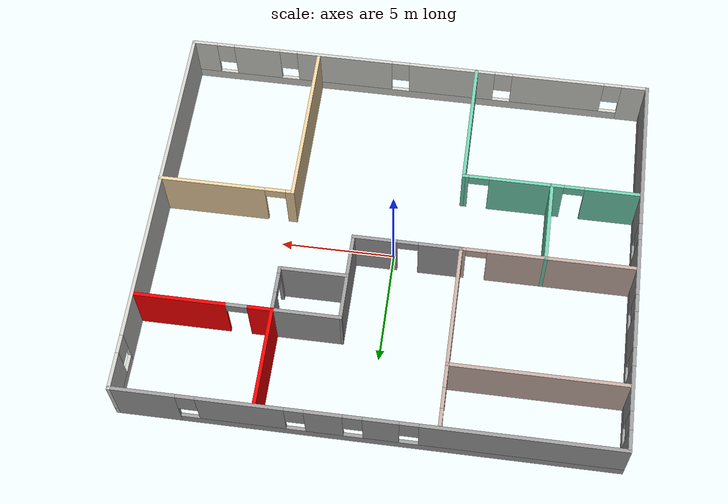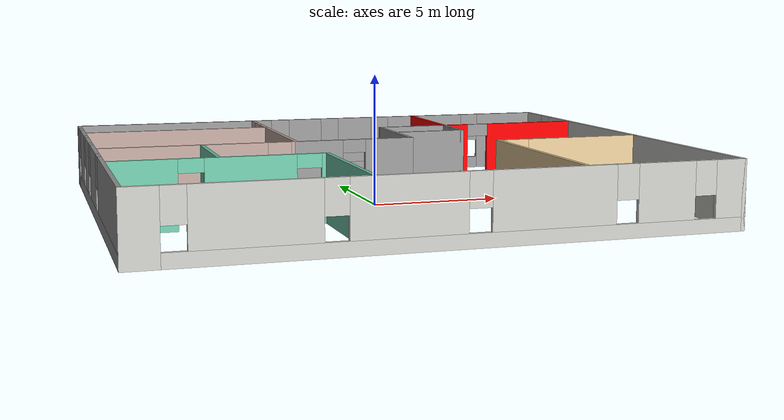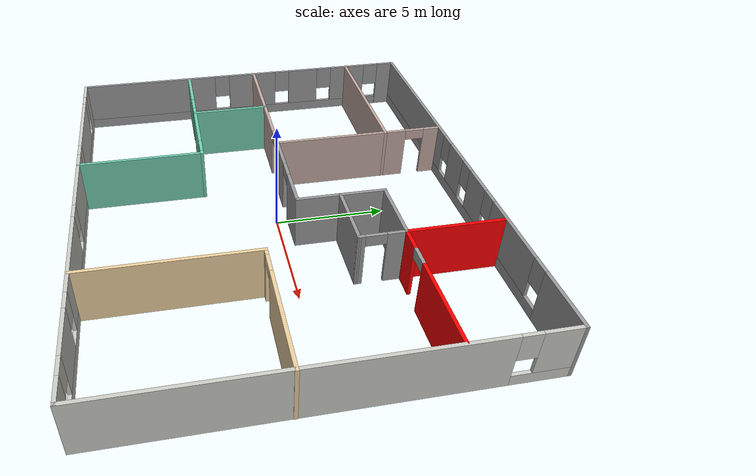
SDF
<?xml version='1.0'?>
<sdf version='1.6'>
  <model name='Building'>
    <link name='Wall_1'>
      <pose frame=''>-10.4348 0 0 0 0 -1.5708</pose>
      <self_collide>0</self_collide>
      <kinematic>0</kinematic>
      <gravity>1</gravity>
      <inertial>
        <mass>1</mass>
        <pose frame=''>0 0 0 0 -0 0</pose>
        <inertia>
          <ixx>1</ixx>
          <ixy>0</ixy>
          <ixz>0</ixz>
          <iyy>1</iyy>
          <iyz>0</iyz>
          <izz>1</izz>
        </inertia>
      </inertial>
      <visual name='Wall_1_Visual_8'>
        <pose frame=''>-2.17654 0 1.9 0 -0 0</pose>
        <geometry>
          <box>
            <size>0.8 0.15 1.2</size>
          </box>
        </geometry>
        <material>
          <script>
            <uri>file://media/materials/scripts/gazebo.material</uri>
            <name>Gazebo/Grey</name>
          </script>
          <ambient>0.5 0.5 0.5 1</ambient>
          <shader type='pixel'>
            <normal_map>__default__</normal_map>
          </shader>
          <diffuse>0.7 0.7 0.7 1</diffuse>
          <specular>0.01 0.01 0.01 1</specular>
          <emissive>0 0 0 1</emissive>
        </material>
        <meta>
          <layer>0</layer>
        </meta>
        <transparency>0</transparency>
        <cast_shadows>1</cast_shadows>
      </visual>
      <visual name='Wall_1_Visual_3'>
        <pose frame=''>-3.3971 0 1.5 0 -0 0</pose>
        <geometry>
          <box>
            <size>1.64112 0.15 2</size>
          </box>
        </geometry>
        <material>
          <script>
            <uri>file://media/materials/scripts/gazebo.material</uri>
            <name>Gazebo/Grey</name>
          </script>
          <ambient>0.5 0.5 0.5 1</ambient>
          <shader type='pixel'>
            <normal_map>__default__</normal_map>
          </shader>
          <diffuse>0.7 0.7 0.7 1</diffuse>
          <specular>0.01 0.01 0.01 1</specular>
          <emissive>0 0 0 1</emissive>
        </material>
        <meta>
          <layer>0</layer>
        </meta>
        <transparency>0</transparency>
        <cast_shadows>1</cast_shadows>
      </visual>
      <visual name='Wall_1_Visual_6'>
        <pose frame=''>-7.38426 0 1.9 0 -0 0</pose>
        <geometry>
          <box>
            <size>0.8 0.15 1.2</size>
          </box>
        </geometry>
        <material>
          <script>
            <uri>file://media/materials/scripts/gazebo.material</uri>
            <name>Gazebo/Grey</name>
          </script>
          <ambient>0.5 0.5 0.5 1</ambient>
          <shader type='pixel'>
            <normal_map>__default__</normal_map>
          </shader>
          <diffuse>0.7 0.7 0.7 1</diffuse>
          <specular>0.01 0.01 0.01 1</specular>
          <emissive>0 0 0 1</emissive>
        </material>
        <meta>
          <layer>0</layer>
        </meta>
        <transparency>0</transparency>
        <cast_shadows>1</cast_shadows>
      </visual>
      <visual name='Wall_1_Visual_2'>
        <pose frame=''>-6.00096 0 1.5 0 -0 0</pose>
        <geometry>
          <box>
            <size>1.9666 0.15 2</size>
          </box>
        </geometry>
        <material>
          <script>
            <uri>file://media/materials/scripts/gazebo.material</uri>
            <name>Gazebo/Grey</name>
          </script>
          <ambient>0.5 0.5 0.5 1</ambient>
          <shader type='pixel'>
            <normal_map>__default__</normal_map>
          </shader>
          <diffuse>0.7 0.7 0.7 1</diffuse>
          <specular>0.01 0.01 0.01 1</specular>
          <emissive>0 0 0 1</emissive>
        </material>
        <meta>
          <layer>0</layer>
        </meta>
        <transparency>0</transparency>
        <cast_shadows>1</cast_shadows>
      </visual>
      <visual name='Wall_1_Visual_1'>
        <pose frame=''>0.482871 0 0.25 0 -0 0</pose>
        <geometry>
          <box>
            <size>16.5043 0.15 0.5</size>
          </box>
        </geometry>
        <material>
          <script>
            <uri>file://media/materials/scripts/gazebo.material</uri>
            <name>Gazebo/Grey</name>
          </script>
          <ambient>0.5 0.5 0.5 1</ambient>
          <shader type='pixel'>
            <normal_map>__default__</normal_map>
          </shader>
          <diffuse>0.7 0.7 0.7 1</diffuse>
          <specular>0.01 0.01 0.01 1</specular>
          <emissive>0 0 0 1</emissive>
        </material>
        <meta>
          <layer>0</layer>
        </meta>
        <transparency>0</transparency>
        <cast_shadows>1</cast_shadows>
      </visual>
      <visual name='Wall_1_Visual_0'>
        <pose frame=''>-8.26713 0 1.25 0 -0 0</pose>
        <geometry>
          <box>
            <size>0.965742 0.15 2.5</size>
          </box>
        </geometry>
        <material>
          <script>
            <uri>file://media/materials/scripts/gazebo.material</uri>
            <name>Gazebo/Grey</name>
          </script>
          <ambient>0.5 0.5 0.5 1</ambient>
          <shader type='pixel'>
            <normal_map>__default__</normal_map>
          </shader>
          <diffuse>0.7 0.7 0.7 1</diffuse>
          <specular>0.01 0.01 0.01 1</specular>
          <emissive>0 0 0 1</emissive>
        </material>
        <meta>
          <layer>0</layer>
        </meta>
        <transparency>0</transparency>
        <cast_shadows>1</cast_shadows>
      </visual>
      <visual name='Wall_1_Visual_7'>
        <pose frame=''>-4.61766 0 1.9 0 -0 0</pose>
        <geometry>
          <box>
            <size>0.8 0.15 1.2</size>
          </box>
        </geometry>
        <material>
          <script>
            <uri>file://media/materials/scripts/gazebo.material</uri>
            <name>Gazebo/Grey</name>
          </script>
          <ambient>0.5 0.5 0.5 1</ambient>
          <shader type='pixel'>
            <normal_map>__default__</normal_map>
          </shader>
          <diffuse>0.7 0.7 0.7 1</diffuse>
          <specular>0.01 0.01 0.01 1</specular>
          <emissive>0 0 0 1</emissive>
        </material>
        <meta>
          <layer>0</layer>
        </meta>
        <transparency>0</transparency>
        <cast_shadows>1</cast_shadows>
      </visual>
      <visual name='Wall_1_Visual_4'>
        <pose frame=''>-0.467756 0 1.5 0 -0 0</pose>
        <geometry>
          <box>
            <size>2.61757 0.15 2</size>
          </box>
        </geometry>
        <material>
          <script>
            <uri>file://media/materials/scripts/gazebo.material</uri>
            <name>Gazebo/Grey</name>
          </script>
          <ambient>0.5 0.5 0.5 1</ambient>
          <shader type='pixel'>
            <normal_map>__default__</normal_map>
          </shader>
          <diffuse>0.7 0.7 0.7 1</diffuse>
          <specular>0.01 0.01 0.01 1</specular>
          <emissive>0 0 0 1</emissive>
        </material>
        <meta>
          <layer>0</layer>
        </meta>
        <transparency>0</transparency>
        <cast_shadows>1</cast_shadows>
      </visual>
      <visual name='Wall_1_Visual_9'>
        <pose frame=''>1.24103 0 1.9 0 -0 0</pose>
        <geometry>
          <box>
            <size>0.8 0.15 1.2</size>
          </box>
        </geometry>
        <material>
          <script>
            <uri>file://media/materials/scripts/gazebo.material</uri>
            <name>Gazebo/Grey</name>
          </script>
          <ambient>0.5 0.5 0.5 1</ambient>
          <shader type='pixel'>
            <normal_map>__default__</normal_map>
          </shader>
          <diffuse>0.7 0.7 0.7 1</diffuse>
          <specular>0.01 0.01 0.01 1</specular>
          <emissive>0 0 0 1</emissive>
        </material>
        <meta>
          <layer>0</layer>
        </meta>
        <transparency>0</transparency>
        <cast_shadows>1</cast_shadows>
      </visual>
      <visual name='Wall_1_Visual_5'>
        <pose frame=''>5.19551 0 1.5 0 -0 0</pose>
        <geometry>
          <box>
            <size>7.10897 0.15 2</size>
          </box>
        </geometry>
        <material>
          <script>
            <uri>file://media/materials/scripts/gazebo.material</uri>
            <name>Gazebo/Grey</name>
          </script>
          <ambient>0.5 0.5 0.5 1</ambient>
          <shader type='pixel'>
            <normal_map>__default__</normal_map>
          </shader>
          <diffuse>0.7 0.7 0.7 1</diffuse>
          <specular>0.01 0.01 0.01 1</specular>
          <emissive>0 0 0 1</emissive>
        </material>
        <meta>
          <layer>0</layer>
        </meta>
        <transparency>0</transparency>
        <cast_shadows>1</cast_shadows>
      </visual>
      <collision name='Wall_1_Collision_9'>
        <laser_retro>0</laser_retro>
        <max_contacts>10</max_contacts>
        <pose frame=''>1.24103 0 1.9 0 -0 0</pose>
        <geometry>
          <box>
            <size>0.8 0.15 1.2</size>
          </box>
        </geometry>
        <surface>
          <friction>
            <ode>
              <mu>1</mu>
              <mu2>1</mu2>
              <fdir1>0 0 0</fdir1>
              <slip1>0</slip1>
              <slip2>0</slip2>
            </ode>
            <torsional>
              <coefficient>1</coefficient>
              <patch_radius>0</patch_radius>
              <surface_radius>0</surface_radius>
              <use_patch_radius>1</use_patch_radius>
              <ode>
                <slip>0</slip>
              </ode>
            </torsional>
          </friction>
          <bounce>
            <restitution_coefficient>0</restitution_coefficient>
            <threshold>1e+06</threshold>
          </bounce>
          <contact>
            <collide_without_contact>0</collide_without_contact>
            <collide_without_contact_bitmask>1</collide_without_contact_bitmask>
            <collide_bitmask>1</collide_bitmask>
            <ode>
              <soft_cfm>0</soft_cfm>
              <soft_erp>0.2</soft_erp>
              <kp>1e+13</kp>
              <kd>1</kd>
              <max_vel>0.01</max_vel>
              <min_depth>0</min_depth>
            </ode>
            <bullet>
              <split_impulse>1</split_impulse>
              <split_impulse_penetration_threshold>-0.01</split_impulse_penetration_threshold>
              <soft_cfm>0</soft_cfm>
              <soft_erp>0.2</soft_erp>
              <kp>1e+13</kp>
              <kd>1</kd>
            </bullet>
          </contact>
        </surface>
      </collision>
      <collision name='Wall_1_Collision_8'>
        <laser_retro>0</laser_retro>
        <max_contacts>10</max_contacts>
        <pose frame=''>-2.17654 0 1.9 0 -0 0</pose>
        <geometry>
          <box>
            <size>0.8 0.15 1.2</size>
          </box>
        </geometry>
        <surface>
          <friction>
            <ode>
              <mu>1</mu>
              <mu2>1</mu2>
              <fdir1>0 0 0</fdir1>
              <slip1>0</slip1>
              <slip2>0</slip2>
            </ode>
            <torsional>
              <coefficient>1</coefficient>
              <patch_radius>0</patch_radius>
              <surface_radius>0</surface_radius>
              <use_patch_radius>1</use_patch_radius>
              <ode>
                <slip>0</slip>
              </ode>
            </torsional>
          </friction>
          <bounce>
            <restitution_coefficient>0</restitution_coefficient>
            <threshold>1e+06</threshold>
          </bounce>
          <contact>
            <collide_without_contact>0</collide_without_contact>
            <collide_without_contact_bitmask>1</collide_without_contact_bitmask>
            <collide_bitmask>1</collide_bitmask>
            <ode>
              <soft_cfm>0</soft_cfm>
              <soft_erp>0.2</soft_erp>
              <kp>1e+13</kp>
              <kd>1</kd>
              <max_vel>0.01</max_vel>
              <min_depth>0</min_depth>
            </ode>
            <bullet>
              <split_impulse>1</split_impulse>
              <split_impulse_penetration_threshold>-0.01</split_impulse_penetration_threshold>
              <soft_cfm>0</soft_cfm>
              <soft_erp>0.2</soft_erp>
              <kp>1e+13</kp>
              <kd>1</kd>
            </bullet>
          </contact>
        </surface>
      </collision>
      <collision name='Wall_1_Collision_5'>
        <laser_retro>0</laser_retro>
        <max_contacts>10</max_contacts>
        <pose frame=''>5.19551 0 1.5 0 -0 0</pose>
        <geometry>
          <box>
            <size>7.10897 0.15 2</size>
          </box>
        </geometry>
        <surface>
          <friction>
            <ode>
              <mu>1</mu>
              <mu2>1</mu2>
              <fdir1>0 0 0</fdir1>
              <slip1>0</slip1>
              <slip2>0</slip2>
            </ode>
            <torsional>
              <coefficient>1</coefficient>
              <patch_radius>0</patch_radius>
              <surface_radius>0</surface_radius>
              <use_patch_radius>1</use_patch_radius>
              <ode>
                <slip>0</slip>
              </ode>
            </torsional>
          </friction>
          <bounce>
            <restitution_coefficient>0</restitution_coefficient>
            <threshold>1e+06</threshold>
          </bounce>
          <contact>
            <collide_without_contact>0</collide_without_contact>
            <collide_without_contact_bitmask>1</collide_without_contact_bitmask>
            <collide_bitmask>1</collide_bitmask>
            <ode>
              <soft_cfm>0</soft_cfm>
              <soft_erp>0.2</soft_erp>
              <kp>1e+13</kp>
              <kd>1</kd>
              <max_vel>0.01</max_vel>
              <min_depth>0</min_depth>
            </ode>
            <bullet>
              <split_impulse>1</split_impulse>
              <split_impulse_penetration_threshold>-0.01</split_impulse_penetration_threshold>
              <soft_cfm>0</soft_cfm>
              <soft_erp>0.2</soft_erp>
              <kp>1e+13</kp>
              <kd>1</kd>
            </bullet>
          </contact>
        </surface>
      </collision>
      <collision name='Wall_1_Collision_6'>
        <laser_retro>0</laser_retro>
        <max_contacts>10</max_contacts>
        <pose frame=''>-7.38426 0 1.9 0 -0 0</pose>
        <geometry>
          <box>
            <size>0.8 0.15 1.2</size>
          </box>
        </geometry>
        <surface>
          <friction>
            <ode>
              <mu>1</mu>
              <mu2>1</mu2>
              <fdir1>0 0 0</fdir1>
              <slip1>0</slip1>
              <slip2>0</slip2>
            </ode>
            <torsional>
              <coefficient>1</coefficient>
              <patch_radius>0</patch_radius>
              <surface_radius>0</surface_radius>
              <use_patch_radius>1</use_patch_radius>
              <ode>
                <slip>0</slip>
              </ode>
            </torsional>
          </friction>
          <bounce>
            <restitution_coefficient>0</restitution_coefficient>
            <threshold>1e+06</threshold>
          </bounce>
          <contact>
            <collide_without_contact>0</collide_without_contact>
            <collide_without_contact_bitmask>1</collide_without_contact_bitmask>
            <collide_bitmask>1</collide_bitmask>
            <ode>
              <soft_cfm>0</soft_cfm>
              <soft_erp>0.2</soft_erp>
              <kp>1e+13</kp>
              <kd>1</kd>
              <max_vel>0.01</max_vel>
              <min_depth>0</min_depth>
            </ode>
            <bullet>
              <split_impulse>1</split_impulse>
              <split_impulse_penetration_threshold>-0.01</split_impulse_penetration_threshold>
              <soft_cfm>0</soft_cfm>
              <soft_erp>0.2</soft_erp>
              <kp>1e+13</kp>
              <kd>1</kd>
            </bullet>
          </contact>
        </surface>
      </collision>
      <collision name='Wall_1_Collision_0'>
        <laser_retro>0</laser_retro>
        <max_contacts>10</max_contacts>
        <pose frame=''>-8.26713 0 1.25 0 -0 0</pose>
        <geometry>
          <box>
            <size>0.965742 0.15 2.5</size>
          </box>
        </geometry>
        <surface>
          <friction>
            <ode>
              <mu>1</mu>
              <mu2>1</mu2>
              <fdir1>0 0 0</fdir1>
              <slip1>0</slip1>
              <slip2>0</slip2>
            </ode>
            <torsional>
              <coefficient>1</coefficient>
              <patch_radius>0</patch_radius>
              <surface_radius>0</surface_radius>
              <use_patch_radius>1</use_patch_radius>
              <ode>
                <slip>0</slip>
              </ode>
            </torsional>
          </friction>
          <bounce>
            <restitution_coefficient>0</restitution_coefficient>
            <threshold>1e+06</threshold>
          </bounce>
          <contact>
            <collide_without_contact>0</collide_without_contact>
            <collide_without_contact_bitmask>1</collide_without_contact_bitmask>
            <collide_bitmask>1</collide_bitmask>
            <ode>
              <soft_cfm>0</soft_cfm>
              <soft_erp>0.2</soft_erp>
              <kp>1e+13</kp>
              <kd>1</kd>
              <max_vel>0.01</max_vel>
              <min_depth>0</min_depth>
            </ode>
            <bullet>
              <split_impulse>1</split_impulse>
              <split_impulse_penetration_threshold>-0.01</split_impulse_penetration_threshold>
              <soft_cfm>0</soft_cfm>
              <soft_erp>0.2</soft_erp>
              <kp>1e+13</kp>
              <kd>1</kd>
            </bullet>
          </contact>
        </surface>
      </collision>
      <collision name='Wall_1_Collision_1'>
        <laser_retro>0</laser_retro>
        <max_contacts>10</max_contacts>
        <pose frame=''>0.482871 0 0.25 0 -0 0</pose>
        <geometry>
          <box>
            <size>16.5343 0.15 0.5</size>
          </box>
        </geometry>
        <surface>
          <friction>
            <ode>
              <mu>1</mu>
              <mu2>1</mu2>
              <fdir1>0 0 0</fdir1>
              <slip1>0</slip1>
              <slip2>0</slip2>
            </ode>
            <torsional>
              <coefficient>1</coefficient>
              <patch_radius>0</patch_radius>
              <surface_radius>0</surface_radius>
              <use_patch_radius>1</use_patch_radius>
              <ode>
                <slip>0</slip>
              </ode>
            </torsional>
          </friction>
          <bounce>
            <restitution_coefficient>0</restitution_coefficient>
            <threshold>1e+06</threshold>
          </bounce>
          <contact>
            <collide_without_contact>0</collide_without_contact>
            <collide_without_contact_bitmask>1</collide_without_contact_bitmask>
            <collide_bitmask>1</collide_bitmask>
            <ode>
              <soft_cfm>0</soft_cfm>
              <soft_erp>0.2</soft_erp>
              <kp>1e+13</kp>
              <kd>1</kd>
              <max_vel>0.01</max_vel>
              <min_depth>0</min_depth>
            </ode>
            <bullet>
              <split_impulse>1</split_impulse>
              <split_impulse_penetration_threshold>-0.01</split_impulse_penetration_threshold>
              <soft_cfm>0</soft_cfm>
              <soft_erp>0.2</soft_erp>
              <kp>1e+13</kp>
              <kd>1</kd>
            </bullet>
          </contact>
        </surface>
      </collision>
      <collision name='Wall_1_Collision_4'>
        <laser_retro>0</laser_retro>
        <max_contacts>10</max_contacts>
        <pose frame=''>-0.467756 0 1.5 0 -0 0</pose>
        <geometry>
          <box>
            <size>2.61757 0.15 2</size>
          </box>
        </geometry>
        <surface>
          <friction>
            <ode>
              <mu>1</mu>
              <mu2>1</mu2>
              <fdir1>0 0 0</fdir1>
              <slip1>0</slip1>
              <slip2>0</slip2>
            </ode>
            <torsional>
              <coefficient>1</coefficient>
              <patch_radius>0</patch_radius>
              <surface_radius>0</surface_radius>
              <use_patch_radius>1</use_patch_radius>
              <ode>
                <slip>0</slip>
              </ode>
            </torsional>
          </friction>
          <bounce>
            <restitution_coefficient>0</restitution_coefficient>
            <threshold>1e+06</threshold>
          </bounce>
          <contact>
            <collide_without_contact>0</collide_without_contact>
            <collide_without_contact_bitmask>1</collide_without_contact_bitmask>
            <collide_bitmask>1</collide_bitmask>
            <ode>
              <soft_cfm>0</soft_cfm>
              <soft_erp>0.2</soft_erp>
              <kp>1e+13</kp>
              <kd>1</kd>
              <max_vel>0.01</max_vel>
              <min_depth>0</min_depth>
            </ode>
            <bullet>
              <split_impulse>1</split_impulse>
              <split_impulse_penetration_threshold>-0.01</split_impulse_penetration_threshold>
              <soft_cfm>0</soft_cfm>
              <soft_erp>0.2</soft_erp>
              <kp>1e+13</kp>
              <kd>1</kd>
            </bullet>
          </contact>
        </surface>
      </collision>
      <collision name='Wall_1_Collision_7'>
        <laser_retro>0</laser_retro>
        <max_contacts>10</max_contacts>
        <pose frame=''>-4.61766 0 1.9 0 -0 0</pose>
        <geometry>
          <box>
            <size>0.8 0.15 1.2</size>
          </box>
        </geometry>
        <surface>
          <friction>
            <ode>
              <mu>1</mu>
              <mu2>1</mu2>
              <fdir1>0 0 0</fdir1>
              <slip1>0</slip1>
              <slip2>0</slip2>
            </ode>
            <torsional>
              <coefficient>1</coefficient>
              <patch_radius>0</patch_radius>
              <surface_radius>0</surface_radius>
              <use_patch_radius>1</use_patch_radius>
              <ode>
                <slip>0</slip>
              </ode>
            </torsional>
          </friction>
          <bounce>
            <restitution_coefficient>0</restitution_coefficient>
            <threshold>1e+06</threshold>
          </bounce>
          <contact>
            <collide_without_contact>0</collide_without_contact>
            <collide_without_contact_bitmask>1</collide_without_contact_bitmask>
            <collide_bitmask>1</collide_bitmask>
            <ode>
              <soft_cfm>0</soft_cfm>
              <soft_erp>0.2</soft_erp>
              <kp>1e+13</kp>
              <kd>1</kd>
              <max_vel>0.01</max_vel>
              <min_depth>0</min_depth>
            </ode>
            <bullet>
              <split_impulse>1</split_impulse>
              <split_impulse_penetration_threshold>-0.01</split_impulse_penetration_threshold>
              <soft_cfm>0</soft_cfm>
              <soft_erp>0.2</soft_erp>
              <kp>1e+13</kp>
              <kd>1</kd>
            </bullet>
          </contact>
        </surface>
      </collision>
      <collision name='Wall_1_Collision_3'>
        <laser_retro>0</laser_retro>
        <max_contacts>10</max_contacts>
        <pose frame=''>-3.3971 0 1.5 0 -0 0</pose>
        <geometry>
          <box>
            <size>1.64112 0.15 2</size>
          </box>
        </geometry>
        <surface>
          <friction>
            <ode>
              <mu>1</mu>
              <mu2>1</mu2>
              <fdir1>0 0 0</fdir1>
              <slip1>0</slip1>
              <slip2>0</slip2>
            </ode>
            <torsional>
              <coefficient>1</coefficient>
              <patch_radius>0</patch_radius>
              <surface_radius>0</surface_radius>
              <use_patch_radius>1</use_patch_radius>
              <ode>
                <slip>0</slip>
              </ode>
            </torsional>
          </friction>
          <bounce>
            <restitution_coefficient>0</restitution_coefficient>
            <threshold>1e+06</threshold>
          </bounce>
          <contact>
            <collide_without_contact>0</collide_without_contact>
            <collide_without_contact_bitmask>1</collide_without_contact_bitmask>
            <collide_bitmask>1</collide_bitmask>
            <ode>
              <soft_cfm>0</soft_cfm>
              <soft_erp>0.2</soft_erp>
              <kp>1e+13</kp>
              <kd>1</kd>
              <max_vel>0.01</max_vel>
              <min_depth>0</min_depth>
            </ode>
            <bullet>
              <split_impulse>1</split_impulse>
              <split_impulse_penetration_threshold>-0.01</split_impulse_penetration_threshold>
              <soft_cfm>0</soft_cfm>
              <soft_erp>0.2</soft_erp>
              <kp>1e+13</kp>
              <kd>1</kd>
            </bullet>
          </contact>
        </surface>
      </collision>
      <collision name='Wall_1_Collision_2'>
        <laser_retro>0</laser_retro>
        <max_contacts>10</max_contacts>
        <pose frame=''>-6.00096 0 1.5 0 -0 0</pose>
        <geometry>
          <box>
            <size>1.9666 0.15 2</size>
          </box>
        </geometry>
        <surface>
          <friction>
            <ode>
              <mu>1</mu>
              <mu2>1</mu2>
              <fdir1>0 0 0</fdir1>
              <slip1>0</slip1>
              <slip2>0</slip2>
            </ode>
            <torsional>
              <coefficient>1</coefficient>
              <patch_radius>0</patch_radius>
              <surface_radius>0</surface_radius>
              <use_patch_radius>1</use_patch_radius>
              <ode>
                <slip>0</slip>
              </ode>
            </torsional>
          </friction>
          <bounce>
            <restitution_coefficient>0</restitution_coefficient>
            <threshold>1e+06</threshold>
          </bounce>
          <contact>
            <collide_without_contact>0</collide_without_contact>
            <collide_without_contact_bitmask>1</collide_without_contact_bitmask>
            <collide_bitmask>1</collide_bitmask>
            <ode>
              <soft_cfm>0</soft_cfm>
              <soft_erp>0.2</soft_erp>
              <kp>1e+13</kp>
              <kd>1</kd>
              <max_vel>0.01</max_vel>
              <min_depth>0</min_depth>
            </ode>
            <bullet>
              <split_impulse>1</split_impulse>
              <split_impulse_penetration_threshold>-0.01</split_impulse_penetration_threshold>
              <soft_cfm>0</soft_cfm>
              <soft_erp>0.2</soft_erp>
              <kp>1e+13</kp>
              <kd>1</kd>
            </bullet>
          </contact>
        </surface>
      </collision>
    </link>
    <link name='Wall_10'>
      <pose frame=''>-8.46331 0.559038 0 0 -0 3.14159</pose>
      <self_collide>0</self_collide>
      <kinematic>0</kinematic>
      <visual name='Wall_10_Visual'>
        <pose frame=''>0 0 1.25 0 -0 0</pose>
        <geometry>
          <box>
            <size>4 0.15 2.5</size>
          </box>
        </geometry>
        <material>
          <script>
            <uri>file://media/materials/scripts/gazebo.material</uri>
            <name>Gazebo/Grey</name>
          </script>
          <ambient>0.760784 0.662745 0.627451 1</ambient>
          <shader type='pixel'/>
          <diffuse>0.7 0.7 0.7 1</diffuse>
          <specular>0.01 0.01 0.01 1</specular>
          <emissive>0 0 0 1</emissive>
        </material>
        <meta>
          <layer>0</layer>
        </meta>
        <transparency>0</transparency>
        <cast_shadows>1</cast_shadows>
      </visual>
      <collision name='Wall_10_Collision'>
        <laser_retro>0</laser_retro>
        <max_contacts>10</max_contacts>
        <pose frame=''>0 0 1.25 0 -0 0</pose>
        <geometry>
          <box>
            <size>4 0.15 2.5</size>
          </box>
        </geometry>
        <surface>
          <friction>
            <ode>
              <mu>1</mu>
              <mu2>1</mu2>
              <fdir1>0 0 0</fdir1>
              <slip1>0</slip1>
              <slip2>0</slip2>
            </ode>
            <torsional>
              <coefficient>1</coefficient>
              <patch_radius>0</patch_radius>
              <surface_radius>0</surface_radius>
              <use_patch_radius>1</use_patch_radius>
              <ode>
                <slip>0</slip>
              </ode>
            </torsional>
          </friction>
          <bounce>
            <restitution_coefficient>0</restitution_coefficient>
            <threshold>1e+06</threshold>
          </bounce>
          <contact>
            <collide_without_contact>0</collide_without_contact>
            <collide_without_contact_bitmask>1</collide_without_contact_bitmask>
            <collide_bitmask>1</collide_bitmask>
            <ode>
              <soft_cfm>0</soft_cfm>
              <soft_erp>0.2</soft_erp>
              <kp>1e+13</kp>
              <kd>1</kd>
              <max_vel>0.01</max_vel>
              <min_depth>0</min_depth>
            </ode>
            <bullet>
              <split_impulse>1</split_impulse>
              <split_impulse_penetration_threshold>-0.01</split_impulse_penetration_threshold>
              <soft_cfm>0</soft_cfm>
              <soft_erp>0.2</soft_erp>
              <kp>1e+13</kp>
              <kd>1</kd>
            </bullet>
          </contact>
        </surface>
      </collision>
    </link>
    <link name='Wall_12'>
      <pose frame=''>-4.73832 0.559038 0 0 -0 0</pose>
      <self_collide>0</self_collide>
      <kinematic>0</kinematic>
      <visual name='Wall_12_Visual_1'>
        <pose frame=''>1.73227 0 1.25 0 -0 0</pose>
        <geometry>
          <box>
            <size>0.285456 0.15 2.5</size>
          </box>
        </geometry>
        <material>
          <script>
            <uri>file://media/materials/scripts/gazebo.material</uri>
            <name>Gazebo/Grey</name>
          </script>
          <ambient>0.760784 0.662745 0.627451 1</ambient>
          <shader type='pixel'/>
          <diffuse>0.7 0.7 0.7 1</diffuse>
          <specular>0.01 0.01 0.01 1</specular>
          <emissive>0 0 0 1</emissive>
        </material>
        <meta>
          <layer>0</layer>
        </meta>
        <transparency>0</transparency>
        <cast_shadows>1</cast_shadows>
      </visual>
      <visual name='Wall_12_Visual_2'>
        <pose frame=''>1.13954 0 2.25 0 -0 0</pose>
        <geometry>
          <box>
            <size>0.9 0.15 0.5</size>
          </box>
        </geometry>
        <material>
          <script>
            <uri>file://media/materials/scripts/gazebo.material</uri>
            <name>Gazebo/Grey</name>
          </script>
          <ambient>0.760784 0.662745 0.627451 1</ambient>
          <shader type='pixel'/>
          <diffuse>0.7 0.7 0.7 1</diffuse>
          <specular>0.01 0.01 0.01 1</specular>
          <emissive>0 0 0 1</emissive>
        </material>
        <meta>
          <layer>0</layer>
        </meta>
        <transparency>0</transparency>
        <cast_shadows>1</cast_shadows>
      </visual>
      <visual name='Wall_12_Visual_0'>
        <pose frame=''>-0.592728 0 1.25 0 -0 0</pose>
        <geometry>
          <box>
            <size>2.56454 0.15 2.5</size>
          </box>
        </geometry>
        <material>
          <script>
            <uri>file://media/materials/scripts/gazebo.material</uri>
            <name>Gazebo/Grey</name>
          </script>
          <ambient>0.760784 0.662745 0.627451 1</ambient>
          <shader type='pixel'/>
          <diffuse>0.7 0.7 0.7 1</diffuse>
          <specular>0.01 0.01 0.01 1</specular>
          <emissive>0 0 0 1</emissive>
        </material>
        <meta>
          <layer>0</layer>
        </meta>
        <transparency>0</transparency>
        <cast_shadows>1</cast_shadows>
      </visual>
      <collision name='Wall_12_Collision_2'>
        <laser_retro>0</laser_retro>
        <max_contacts>10</max_contacts>
        <pose frame=''>1.13954 0 2.25 0 -0 0</pose>
        <geometry>
          <box>
            <size>0.9 0.15 0.5</size>
          </box>
        </geometry>
        <surface>
          <friction>
            <ode>
              <mu>1</mu>
              <mu2>1</mu2>
              <fdir1>0 0 0</fdir1>
              <slip1>0</slip1>
              <slip2>0</slip2>
            </ode>
            <torsional>
              <coefficient>1</coefficient>
              <patch_radius>0</patch_radius>
              <surface_radius>0</surface_radius>
              <use_patch_radius>1</use_patch_radius>
              <ode>
                <slip>0</slip>
              </ode>
            </torsional>
          </friction>
          <bounce>
            <restitution_coefficient>0</restitution_coefficient>
            <threshold>1e+06</threshold>
          </bounce>
          <contact>
            <collide_without_contact>0</collide_without_contact>
            <collide_without_contact_bitmask>1</collide_without_contact_bitmask>
            <collide_bitmask>1</collide_bitmask>
            <ode>
              <soft_cfm>0</soft_cfm>
              <soft_erp>0.2</soft_erp>
              <kp>1e+13</kp>
              <kd>1</kd>
              <max_vel>0.01</max_vel>
              <min_depth>0</min_depth>
            </ode>
            <bullet>
              <split_impulse>1</split_impulse>
              <split_impulse_penetration_threshold>-0.01</split_impulse_penetration_threshold>
              <soft_cfm>0</soft_cfm>
              <soft_erp>0.2</soft_erp>
              <kp>1e+13</kp>
              <kd>1</kd>
            </bullet>
          </contact>
        </surface>
      </collision>
      <collision name='Wall_12_Collision_1'>
        <laser_retro>0</laser_retro>
        <max_contacts>10</max_contacts>
        <pose frame=''>1.73227 0 1.25 0 -0 0</pose>
        <geometry>
          <box>
            <size>0.285456 0.15 2.5</size>
          </box>
        </geometry>
        <surface>
          <friction>
            <ode>
              <mu>1</mu>
              <mu2>1</mu2>
              <fdir1>0 0 0</fdir1>
              <slip1>0</slip1>
              <slip2>0</slip2>
            </ode>
            <torsional>
              <coefficient>1</coefficient>
              <patch_radius>0</patch_radius>
              <surface_radius>0</surface_radius>
              <use_patch_radius>1</use_patch_radius>
              <ode>
                <slip>0</slip>
              </ode>
            </torsional>
          </friction>
          <bounce>
            <restitution_coefficient>0</restitution_coefficient>
            <threshold>1e+06</threshold>
          </bounce>
          <contact>
            <collide_without_contact>0</collide_without_contact>
            <collide_without_contact_bitmask>1</collide_without_contact_bitmask>
            <collide_bitmask>1</collide_bitmask>
            <ode>
              <soft_cfm>0</soft_cfm>
              <soft_erp>0.2</soft_erp>
              <kp>1e+13</kp>
              <kd>1</kd>
              <max_vel>0.01</max_vel>
              <min_depth>0</min_depth>
            </ode>
            <bullet>
              <split_impulse>1</split_impulse>
              <split_impulse_penetration_threshold>-0.01</split_impulse_penetration_threshold>
              <soft_cfm>0</soft_cfm>
              <soft_erp>0.2</soft_erp>
              <kp>1e+13</kp>
              <kd>1</kd>
            </bullet>
          </contact>
        </surface>
      </collision>
      <collision name='Wall_12_Collision_0'>
        <laser_retro>0</laser_retro>
        <max_contacts>10</max_contacts>
        <pose frame=''>-0.592728 0 1.25 0 -0 0</pose>
        <geometry>
          <box>
            <size>2.56454 0.15 2.5</size>
          </box>
        </geometry>
        <surface>
          <friction>
            <ode>
              <mu>1</mu>
              <mu2>1</mu2>
              <fdir1>0 0 0</fdir1>
              <slip1>0</slip1>
              <slip2>0</slip2>
            </ode>
            <torsional>
              <coefficient>1</coefficient>
              <patch_radius>0</patch_radius>
              <surface_radius>0</surface_radius>
              <use_patch_radius>1</use_patch_radius>
              <ode>
                <slip>0</slip>
              </ode>
            </torsional>
          </friction>
          <bounce>
            <restitution_coefficient>0</restitution_coefficient>
            <threshold>1e+06</threshold>
          </bounce>
          <contact>
            <collide_without_contact>0</collide_without_contact>
            <collide_without_contact_bitmask>1</collide_without_contact_bitmask>
            <collide_bitmask>1</collide_bitmask>
            <ode>
              <soft_cfm>0</soft_cfm>
              <soft_erp>0.2</soft_erp>
              <kp>1e+13</kp>
              <kd>1</kd>
              <max_vel>0.01</max_vel>
              <min_depth>0</min_depth>
            </ode>
            <bullet>
              <split_impulse>1</split_impulse>
              <split_impulse_penetration_threshold>-0.01</split_impulse_penetration_threshold>
              <soft_cfm>0</soft_cfm>
              <soft_erp>0.2</soft_erp>
              <kp>1e+13</kp>
              <kd>1</kd>
            </bullet>
          </contact>
        </surface>
      </collision>
    </link>
    <link name='Wall_13'>
      <pose frame=''>-2.93835 3.23415 0 0 -0 1.57081</pose>
      <self_collide>0</self_collide>
      <kinematic>0</kinematic>
      <visual name='Wall_13_Visual'>
        <pose frame=''>0 0 1.25 0 -0 0</pose>
        <geometry>
          <box>
            <size>5.5 0.15 2.5</size>
          </box>
        </geometry>
        <material>
          <script>
            <uri>file://media/materials/scripts/gazebo.material</uri>
            <name>Gazebo/Grey</name>
          </script>
          <ambient>0.760784 0.662745 0.627451 1</ambient>
          <shader type='pixel'/>
          <diffuse>0.7 0.7 0.7 1</diffuse>
          <specular>0.01 0.01 0.01 1</specular>
          <emissive>0 0 0 1</emissive>
        </material>
        <meta>
          <layer>0</layer>
        </meta>
        <transparency>0</transparency>
        <cast_shadows>1</cast_shadows>
      </visual>
      <collision name='Wall_13_Collision'>
        <laser_retro>0</laser_retro>
        <max_contacts>10</max_contacts>
        <pose frame=''>0 0 1.25 0 -0 0</pose>
        <geometry>
          <box>
            <size>5.5 0.15 2.5</size>
          </box>
        </geometry>
        <surface>
          <friction>
            <ode>
              <mu>1</mu>
              <mu2>1</mu2>
              <fdir1>0 0 0</fdir1>
              <slip1>0</slip1>
              <slip2>0</slip2>
            </ode>
            <torsional>
              <coefficient>1</coefficient>
              <patch_radius>0</patch_radius>
              <surface_radius>0</surface_radius>
              <use_patch_radius>1</use_patch_radius>
              <ode>
                <slip>0</slip>
              </ode>
            </torsional>
          </friction>
          <bounce>
            <restitution_coefficient>0</restitution_coefficient>
            <threshold>1e+06</threshold>
          </bounce>
          <contact>
            <collide_without_contact>0</collide_without_contact>
            <collide_without_contact_bitmask>1</collide_without_contact_bitmask>
            <collide_bitmask>1</collide_bitmask>
            <ode>
              <soft_cfm>0</soft_cfm>
              <soft_erp>0.2</soft_erp>
              <kp>1e+13</kp>
              <kd>1</kd>
              <max_vel>0.01</max_vel>
              <min_depth>0</min_depth>
            </ode>
            <bullet>
              <split_impulse>1</split_impulse>
              <split_impulse_penetration_threshold>-0.01</split_impulse_penetration_threshold>
              <soft_cfm>0</soft_cfm>
              <soft_erp>0.2</soft_erp>
              <kp>1e+13</kp>
              <kd>1</kd>
            </bullet>
          </contact>
        </surface>
      </collision>
    </link>
    <link name='Wall_14'>
      <pose frame=''>-6.61335 5.90915 0 0 0 -3.14156</pose>
      <self_collide>0</self_collide>
      <kinematic>0</kinematic>
      <visual name='Wall_14_Visual'>
        <pose frame=''>0 0 1.25 0 -0 0</pose>
        <geometry>
          <box>
            <size>7.5 0.15 2.5</size>
          </box>
        </geometry>
        <material>
          <script>
            <uri>file://media/materials/scripts/gazebo.material</uri>
            <name>Gazebo/Grey</name>
          </script>
          <ambient>0.760784 0.662745 0.627451 1</ambient>
          <shader type='pixel'/>
          <diffuse>0.7 0.7 0.7 1</diffuse>
          <specular>0.01 0.01 0.01 1</specular>
          <emissive>0 0 0 1</emissive>
        </material>
        <meta>
          <layer>0</layer>
        </meta>
        <transparency>0</transparency>
        <cast_shadows>1</cast_shadows>
      </visual>
      <collision name='Wall_14_Collision'>
        <laser_retro>0</laser_retro>
        <max_contacts>10</max_contacts>
        <pose frame=''>0 0 1.25 0 -0 0</pose>
        <geometry>
          <box>
            <size>7.5 0.15 2.5</size>
          </box>
        </geometry>
        <surface>
          <friction>
            <ode>
              <mu>1</mu>
              <mu2>1</mu2>
              <fdir1>0 0 0</fdir1>
              <slip1>0</slip1>
              <slip2>0</slip2>
            </ode>
            <torsional>
              <coefficient>1</coefficient>
              <patch_radius>0</patch_radius>
              <surface_radius>0</surface_radius>
              <use_patch_radius>1</use_patch_radius>
              <ode>
                <slip>0</slip>
              </ode>
            </torsional>
          </friction>
          <bounce>
            <restitution_coefficient>0</restitution_coefficient>
            <threshold>1e+06</threshold>
          </bounce>
          <contact>
            <collide_without_contact>0</collide_without_contact>
            <collide_without_contact_bitmask>1</collide_without_contact_bitmask>
            <collide_bitmask>1</collide_bitmask>
            <ode>
              <soft_cfm>0</soft_cfm>
              <soft_erp>0.2</soft_erp>
              <kp>1e+13</kp>
              <kd>1</kd>
              <max_vel>0.01</max_vel>
              <min_depth>0</min_depth>
            </ode>
            <bullet>
              <split_impulse>1</split_impulse>
              <split_impulse_penetration_threshold>-0.01</split_impulse_penetration_threshold>
              <soft_cfm>0</soft_cfm>
              <soft_erp>0.2</soft_erp>
              <kp>1e+13</kp>
              <kd>1</kd>
            </bullet>
          </contact>
        </surface>
      </collision>
    </link>
    <link name='Wall_16'>
      <pose frame=''>-2.93838 7.21526 0 0 -0 1.5708</pose>
      <self_collide>0</self_collide>
      <kinematic>0</kinematic>
      <visual name='Wall_16_Visual_1'>
        <pose frame=''>0.999999 0 1.25 0 -0 0</pose>
        <geometry>
          <box>
            <size>0.762002 0.15 2.5</size>
          </box>
        </geometry>
        <material>
          <script>
            <uri>file://media/materials/scripts/gazebo.material</uri>
            <name>Gazebo/Grey</name>
          </script>
          <ambient>0.760784 0.662745 0.627451 1</ambient>
          <shader type='pixel'/>
          <diffuse>0.7 0.7 0.7 1</diffuse>
          <specular>0.01 0.01 0.01 1</specular>
          <emissive>0 0 0 1</emissive>
        </material>
        <meta>
          <layer>0</layer>
        </meta>
        <transparency>0</transparency>
        <cast_shadows>1</cast_shadows>
      </visual>
      <visual name='Wall_16_Visual_2'>
        <pose frame=''>0.168998 0 2.25 0 -0 0</pose>
        <geometry>
          <box>
            <size>0.9 0.15 0.5</size>
          </box>
        </geometry>
        <material>
          <script>
            <uri>file://media/materials/scripts/gazebo.material</uri>
            <name>Gazebo/Grey</name>
          </script>
          <ambient>0.760784 0.662745 0.627451 1</ambient>
          <shader type='pixel'/>
          <diffuse>0.7 0.7 0.7 1</diffuse>
          <specular>0.01 0.01 0.01 1</specular>
          <emissive>0 0 0 1</emissive>
        </material>
        <meta>
          <layer>0</layer>
        </meta>
        <transparency>0</transparency>
        <cast_shadows>1</cast_shadows>
      </visual>
      <visual name='Wall_16_Visual_0'>
        <pose frame=''>-0.831001 0 1.25 0 -0 0</pose>
        <geometry>
          <box>
            <size>1.1 0.15 2.5</size>
          </box>
        </geometry>
        <material>
          <script>
            <uri>file://media/materials/scripts/gazebo.material</uri>
            <name>Gazebo/Grey</name>
          </script>
          <ambient>0.760784 0.662745 0.627451 1</ambient>
          <shader type='pixel'/>
          <diffuse>0.7 0.7 0.7 1</diffuse>
          <specular>0.01 0.01 0.01 1</specular>
          <emissive>0 0 0 1</emissive>
        </material>
        <meta>
          <layer>0</layer>
        </meta>
        <transparency>0</transparency>
        <cast_shadows>1</cast_shadows>
      </visual>
      <collision name='Wall_16_Collision_2'>
        <laser_retro>0</laser_retro>
        <max_contacts>10</max_contacts>
        <pose frame=''>0.168998 0 2.25 0 -0 0</pose>
        <geometry>
          <box>
            <size>0.9 0.15 0.5</size>
          </box>
        </geometry>
        <surface>
          <friction>
            <ode>
              <mu>1</mu>
              <mu2>1</mu2>
              <fdir1>0 0 0</fdir1>
              <slip1>0</slip1>
              <slip2>0</slip2>
            </ode>
            <torsional>
              <coefficient>1</coefficient>
              <patch_radius>0</patch_radius>
              <surface_radius>0</surface_radius>
              <use_patch_radius>1</use_patch_radius>
              <ode>
                <slip>0</slip>
              </ode>
            </torsional>
          </friction>
          <bounce>
            <restitution_coefficient>0</restitution_coefficient>
            <threshold>1e+06</threshold>
          </bounce>
          <contact>
            <collide_without_contact>0</collide_without_contact>
            <collide_without_contact_bitmask>1</collide_without_contact_bitmask>
            <collide_bitmask>1</collide_bitmask>
            <ode>
              <soft_cfm>0</soft_cfm>
              <soft_erp>0.2</soft_erp>
              <kp>1e+13</kp>
              <kd>1</kd>
              <max_vel>0.01</max_vel>
              <min_depth>0</min_depth>
            </ode>
            <bullet>
              <split_impulse>1</split_impulse>
              <split_impulse_penetration_threshold>-0.01</split_impulse_penetration_threshold>
              <soft_cfm>0</soft_cfm>
              <soft_erp>0.2</soft_erp>
              <kp>1e+13</kp>
              <kd>1</kd>
            </bullet>
          </contact>
        </surface>
      </collision>
      <collision name='Wall_16_Collision_0'>
        <laser_retro>0</laser_retro>
        <max_contacts>10</max_contacts>
        <pose frame=''>-0.831001 0 1.25 0 -0 0</pose>
        <geometry>
          <box>
            <size>1.1 0.15 2.5</size>
          </box>
        </geometry>
        <surface>
          <friction>
            <ode>
              <mu>1</mu>
              <mu2>1</mu2>
              <fdir1>0 0 0</fdir1>
              <slip1>0</slip1>
              <slip2>0</slip2>
            </ode>
            <torsional>
              <coefficient>1</coefficient>
              <patch_radius>0</patch_radius>
              <surface_radius>0</surface_radius>
              <use_patch_radius>1</use_patch_radius>
              <ode>
                <slip>0</slip>
              </ode>
            </torsional>
          </friction>
          <bounce>
            <restitution_coefficient>0</restitution_coefficient>
            <threshold>1e+06</threshold>
          </bounce>
          <contact>
            <collide_without_contact>0</collide_without_contact>
            <collide_without_contact_bitmask>1</collide_without_contact_bitmask>
            <collide_bitmask>1</collide_bitmask>
            <ode>
              <soft_cfm>0</soft_cfm>
              <soft_erp>0.2</soft_erp>
              <kp>1e+13</kp>
              <kd>1</kd>
              <max_vel>0.01</max_vel>
              <min_depth>0</min_depth>
            </ode>
            <bullet>
              <split_impulse>1</split_impulse>
              <split_impulse_penetration_threshold>-0.01</split_impulse_penetration_threshold>
              <soft_cfm>0</soft_cfm>
              <soft_erp>0.2</soft_erp>
              <kp>1e+13</kp>
              <kd>1</kd>
            </bullet>
          </contact>
        </surface>
      </collision>
      <collision name='Wall_16_Collision_1'>
        <laser_retro>0</laser_retro>
        <max_contacts>10</max_contacts>
        <pose frame=''>0.999999 0 1.25 0 -0 0</pose>
        <geometry>
          <box>
            <size>0.762002 0.15 2.5</size>
          </box>
        </geometry>
        <surface>
          <friction>
            <ode>
              <mu>1</mu>
              <mu2>1</mu2>
              <fdir1>0 0 0</fdir1>
              <slip1>0</slip1>
              <slip2>0</slip2>
            </ode>
            <torsional>
              <coefficient>1</coefficient>
              <patch_radius>0</patch_radius>
              <surface_radius>0</surface_radius>
              <use_patch_radius>1</use_patch_radius>
              <ode>
                <slip>0</slip>
              </ode>
            </torsional>
          </friction>
          <bounce>
            <restitution_coefficient>0</restitution_coefficient>
            <threshold>1e+06</threshold>
          </bounce>
          <contact>
            <collide_without_contact>0</collide_without_contact>
            <collide_without_contact_bitmask>1</collide_without_contact_bitmask>
            <collide_bitmask>1</collide_bitmask>
            <ode>
              <soft_cfm>0</soft_cfm>
              <soft_erp>0.2</soft_erp>
              <kp>1e+13</kp>
              <kd>1</kd>
              <max_vel>0.01</max_vel>
              <min_depth>0</min_depth>
            </ode>
            <bullet>
              <split_impulse>1</split_impulse>
              <split_impulse_penetration_threshold>-0.01</split_impulse_penetration_threshold>
              <soft_cfm>0</soft_cfm>
              <soft_erp>0.2</soft_erp>
              <kp>1e+13</kp>
              <kd>1</kd>
            </bullet>
          </contact>
        </surface>
      </collision>
    </link>
    <link name='Wall_18'>
      <pose frame=''>4.58481 -4.95144 0 0 -0 1.5708</pose>
      <self_collide>0</self_collide>
      <kinematic>0</kinematic>
      <visual name='Wall_18_Visual'>
        <pose frame=''>0 0 1.25 0 -0 0</pose>
        <geometry>
          <box>
            <size>7.5 0.15 2.5</size>
          </box>
        </geometry>
        <material>
          <script>
            <uri>file://media/materials/scripts/gazebo.material</uri>
            <name>Gazebo/Grey</name>
          </script>
          <ambient>0.921569 0.807843 0.615686 1</ambient>
          <shader type='pixel'/>
          <diffuse>0.7 0.7 0.7 1</diffuse>
          <specular>0.01 0.01 0.01 1</specular>
          <emissive>0 0 0 1</emissive>
        </material>
        <meta>
          <layer>0</layer>
        </meta>
        <transparency>0</transparency>
        <cast_shadows>1</cast_shadows>
      </visual>
      <collision name='Wall_18_Collision'>
        <laser_retro>0</laser_retro>
        <max_contacts>10</max_contacts>
        <pose frame=''>0 0 1.25 0 -0 0</pose>
        <geometry>
          <box>
            <size>7.5 0.15 2.5</size>
          </box>
        </geometry>
        <surface>
          <friction>
            <ode>
              <mu>1</mu>
              <mu2>1</mu2>
              <fdir1>0 0 0</fdir1>
              <slip1>0</slip1>
              <slip2>0</slip2>
            </ode>
            <torsional>
              <coefficient>1</coefficient>
              <patch_radius>0</patch_radius>
              <surface_radius>0</surface_radius>
              <use_patch_radius>1</use_patch_radius>
              <ode>
                <slip>0</slip>
              </ode>
            </torsional>
          </friction>
          <bounce>
            <restitution_coefficient>0</restitution_coefficient>
            <threshold>1e+06</threshold>
          </bounce>
          <contact>
            <collide_without_contact>0</collide_without_contact>
            <collide_without_contact_bitmask>1</collide_without_contact_bitmask>
            <collide_bitmask>1</collide_bitmask>
            <ode>
              <soft_cfm>0</soft_cfm>
              <soft_erp>0.2</soft_erp>
              <kp>1e+13</kp>
              <kd>1</kd>
              <max_vel>0.01</max_vel>
              <min_depth>0</min_depth>
            </ode>
            <bullet>
              <split_impulse>1</split_impulse>
              <split_impulse_penetration_threshold>-0.01</split_impulse_penetration_threshold>
              <soft_cfm>0</soft_cfm>
              <soft_erp>0.2</soft_erp>
              <kp>1e+13</kp>
              <kd>1</kd>
            </bullet>
          </contact>
        </surface>
      </collision>
    </link>
    <link name='Wall_19'>
      <pose frame=''>7.50981 -1.27643 0 0 -0 0</pose>
      <self_collide>0</self_collide>
      <kinematic>0</kinematic>
      <visual name='Wall_19_Visual_1'>
        <pose frame=''>0.646095 0 1.25 0 -0 0</pose>
        <geometry>
          <box>
            <size>4.70781 0.15 2.5</size>
          </box>
        </geometry>
        <material>
          <script>
            <uri>file://media/materials/scripts/gazebo.material</uri>
            <name>Gazebo/Grey</name>
          </script>
          <ambient>0.921569 0.807843 0.615686 1</ambient>
          <shader type='pixel'/>
          <diffuse>0.7 0.7 0.7 1</diffuse>
          <specular>0.01 0.01 0.01 1</specular>
          <emissive>0 0 0 1</emissive>
        </material>
        <meta>
          <layer>0</layer>
        </meta>
        <transparency>0</transparency>
        <cast_shadows>1</cast_shadows>
      </visual>
      <visual name='Wall_19_Visual_2'>
        <pose frame=''>-2.15781 0 2.25 0 -0 0</pose>
        <geometry>
          <box>
            <size>0.9 0.15 0.5</size>
          </box>
        </geometry>
        <material>
          <script>
            <uri>file://media/materials/scripts/gazebo.material</uri>
            <name>Gazebo/Grey</name>
          </script>
          <ambient>0.921569 0.807843 0.615686 1</ambient>
          <shader type='pixel'/>
          <diffuse>0.7 0.7 0.7 1</diffuse>
          <specular>0.01 0.01 0.01 1</specular>
          <emissive>0 0 0 1</emissive>
        </material>
        <meta>
          <layer>0</layer>
        </meta>
        <transparency>0</transparency>
        <cast_shadows>1</cast_shadows>
      </visual>
      <visual name='Wall_19_Visual_0'>
        <pose frame=''>-2.8039 0 1.25 0 -0 0</pose>
        <geometry>
          <box>
            <size>0.39219 0.15 2.5</size>
          </box>
        </geometry>
        <material>
          <script>
            <uri>file://media/materials/scripts/gazebo.material</uri>
            <name>Gazebo/Grey</name>
          </script>
          <ambient>0.921569 0.807843 0.615686 1</ambient>
          <shader type='pixel'/>
          <diffuse>0.7 0.7 0.7 1</diffuse>
          <specular>0.01 0.01 0.01 1</specular>
          <emissive>0 0 0 1</emissive>
        </material>
        <meta>
          <layer>0</layer>
        </meta>
        <transparency>0</transparency>
        <cast_shadows>1</cast_shadows>
      </visual>
      <collision name='Wall_19_Collision_1'>
        <laser_retro>0</laser_retro>
        <max_contacts>10</max_contacts>
        <pose frame=''>0.646095 0 1.25 0 -0 0</pose>
        <geometry>
          <box>
            <size>4.70781 0.15 2.5</size>
          </box>
        </geometry>
        <surface>
          <friction>
            <ode>
              <mu>1</mu>
              <mu2>1</mu2>
              <fdir1>0 0 0</fdir1>
              <slip1>0</slip1>
              <slip2>0</slip2>
            </ode>
            <torsional>
              <coefficient>1</coefficient>
              <patch_radius>0</patch_radius>
              <surface_radius>0</surface_radius>
              <use_patch_radius>1</use_patch_radius>
              <ode>
                <slip>0</slip>
              </ode>
            </torsional>
          </friction>
          <bounce>
            <restitution_coefficient>0</restitution_coefficient>
            <threshold>1e+06</threshold>
          </bounce>
          <contact>
            <collide_without_contact>0</collide_without_contact>
            <collide_without_contact_bitmask>1</collide_without_contact_bitmask>
            <collide_bitmask>1</collide_bitmask>
            <ode>
              <soft_cfm>0</soft_cfm>
              <soft_erp>0.2</soft_erp>
              <kp>1e+13</kp>
              <kd>1</kd>
              <max_vel>0.01</max_vel>
              <min_depth>0</min_depth>
            </ode>
            <bullet>
              <split_impulse>1</split_impulse>
              <split_impulse_penetration_threshold>-0.01</split_impulse_penetration_threshold>
              <soft_cfm>0</soft_cfm>
              <soft_erp>0.2</soft_erp>
              <kp>1e+13</kp>
              <kd>1</kd>
            </bullet>
          </contact>
        </surface>
      </collision>
      <collision name='Wall_19_Collision_0'>
        <laser_retro>0</laser_retro>
        <max_contacts>10</max_contacts>
        <pose frame=''>-2.8039 0 1.25 0 -0 0</pose>
        <geometry>
          <box>
            <size>0.39219 0.15 2.5</size>
          </box>
        </geometry>
        <surface>
          <friction>
            <ode>
              <mu>1</mu>
              <mu2>1</mu2>
              <fdir1>0 0 0</fdir1>
              <slip1>0</slip1>
              <slip2>0</slip2>
            </ode>
            <torsional>
              <coefficient>1</coefficient>
              <patch_radius>0</patch_radius>
              <surface_radius>0</surface_radius>
              <use_patch_radius>1</use_patch_radius>
              <ode>
                <slip>0</slip>
              </ode>
            </torsional>
          </friction>
          <bounce>
            <restitution_coefficient>0</restitution_coefficient>
            <threshold>1e+06</threshold>
          </bounce>
          <contact>
            <collide_without_contact>0</collide_without_contact>
            <collide_without_contact_bitmask>1</collide_without_contact_bitmask>
            <collide_bitmask>1</collide_bitmask>
            <ode>
              <soft_cfm>0</soft_cfm>
              <soft_erp>0.2</soft_erp>
              <kp>1e+13</kp>
              <kd>1</kd>
              <max_vel>0.01</max_vel>
              <min_depth>0</min_depth>
            </ode>
            <bullet>
              <split_impulse>1</split_impulse>
              <split_impulse_penetration_threshold>-0.01</split_impulse_penetration_threshold>
              <soft_cfm>0</soft_cfm>
              <soft_erp>0.2</soft_erp>
              <kp>1e+13</kp>
              <kd>1</kd>
            </bullet>
          </contact>
        </surface>
      </collision>
      <collision name='Wall_19_Collision_2'>
        <laser_retro>0</laser_retro>
        <max_contacts>10</max_contacts>
        <pose frame=''>-2.15781 0 2.25 0 -0 0</pose>
        <geometry>
          <box>
            <size>0.9 0.15 0.5</size>
          </box>
        </geometry>
        <surface>
          <friction>
            <ode>
              <mu>1</mu>
              <mu2>1</mu2>
              <fdir1>0 0 0</fdir1>
              <slip1>0</slip1>
              <slip2>0</slip2>
            </ode>
            <torsional>
              <coefficient>1</coefficient>
              <patch_radius>0</patch_radius>
              <surface_radius>0</surface_radius>
              <use_patch_radius>1</use_patch_radius>
              <ode>
                <slip>0</slip>
              </ode>
            </torsional>
          </friction>
          <bounce>
            <restitution_coefficient>0</restitution_coefficient>
            <threshold>1e+06</threshold>
          </bounce>
          <contact>
            <collide_without_contact>0</collide_without_contact>
            <collide_without_contact_bitmask>1</collide_without_contact_bitmask>
            <collide_bitmask>1</collide_bitmask>
            <ode>
              <soft_cfm>0</soft_cfm>
              <soft_erp>0.2</soft_erp>
              <kp>1e+13</kp>
              <kd>1</kd>
              <max_vel>0.01</max_vel>
              <min_depth>0</min_depth>
            </ode>
            <bullet>
              <split_impulse>1</split_impulse>
              <split_impulse_penetration_threshold>-0.01</split_impulse_penetration_threshold>
              <soft_cfm>0</soft_cfm>
              <soft_erp>0.2</soft_erp>
              <kp>1e+13</kp>
              <kd>1</kd>
            </bullet>
          </contact>
        </surface>
      </collision>
    </link>
    <link name='Wall_2'>
      <pose frame=''>-0.009806 -8.675 0 0 -0 0</pose>
      <inertial>
        <mass>1</mass>
        <pose frame=''>0 0 0 0 -0 0</pose>
        <inertia>
          <ixx>1</ixx>
          <ixy>0</ixy>
          <ixz>0</ixz>
          <iyy>1</iyy>
          <iyz>0</iyz>
          <izz>1</izz>
        </inertia>
      </inertial>
      <self_collide>0</self_collide>
      <kinematic>0</kinematic>
      <gravity>1</gravity>
      <visual name='Wall_2_Visual_7'>
        <pose frame=''>-8.87805 0 1.9 0 -0 0</pose>
        <geometry>
          <box>
            <size>0.8 0.15 1.2</size>
          </box>
        </geometry>
        <material>
          <script>
            <uri>file://media/materials/scripts/gazebo.material</uri>
            <name>Gazebo/CeilingTiled</name>
          </script>
          <ambient>0.5 0.5 0.5 1</ambient>
          <shader type='pixel'>
            <normal_map>__default__</normal_map>
          </shader>
          <diffuse>1 1 1 1</diffuse>
          <specular>0 0 0 1</specular>
          <emissive>0 0 0 1</emissive>
        </material>
        <meta>
          <layer>0</layer>
        </meta>
        <transparency>0</transparency>
        <cast_shadows>1</cast_shadows>
      </visual>
      <visual name='Wall_2_Visual_5'>
        <pose frame=''>7.47744 0 1.5 0 -0 0</pose>
        <geometry>
          <box>
            <size>2.12934 0.15 2</size>
          </box>
        </geometry>
        <material>
          <script>
            <uri>file://media/materials/scripts/gazebo.material</uri>
            <name>Gazebo/CeilingTiled</name>
          </script>
          <ambient>0.5 0.5 0.5 1</ambient>
          <shader type='pixel'>
            <normal_map>__default__</normal_map>
          </shader>
          <diffuse>1 1 1 1</diffuse>
          <specular>0 0 0 1</specular>
          <emissive>0 0 0 1</emissive>
        </material>
        <meta>
          <layer>0</layer>
        </meta>
        <transparency>0</transparency>
        <cast_shadows>1</cast_shadows>
      </visual>
      <visual name='Wall_2_Visual_9'>
        <pose frame=''>0.805049 0 1.9 0 -0 0</pose>
        <geometry>
          <box>
            <size>0.8 0.15 1.2</size>
          </box>
        </geometry>
        <material>
          <script>
            <uri>file://media/materials/scripts/gazebo.material</uri>
            <name>Gazebo/CeilingTiled</name>
          </script>
          <ambient>0.5 0.5 0.5 1</ambient>
          <shader type='pixel'>
            <normal_map>__default__</normal_map>
          </shader>
          <diffuse>1 1 1 1</diffuse>
          <specular>0 0 0 1</specular>
          <emissive>0 0 0 1</emissive>
        </material>
        <meta>
          <layer>0</layer>
        </meta>
        <transparency>0</transparency>
        <cast_shadows>1</cast_shadows>
      </visual>
      <visual name='Wall_2_Visual_8'>
        <pose frame=''>-3.91445 0 1.9 0 -0 0</pose>
        <geometry>
          <box>
            <size>0.8 0.15 1.2</size>
          </box>
        </geometry>
        <material>
          <script>
            <uri>file://media/materials/scripts/gazebo.material</uri>
            <name>Gazebo/CeilingTiled</name>
          </script>
          <ambient>0.5 0.5 0.5 1</ambient>
          <shader type='pixel'>
            <normal_map>__default__</normal_map>
          </shader>
          <diffuse>1 1 1 1</diffuse>
          <specular>0 0 0 1</specular>
          <emissive>0 0 0 1</emissive>
        </material>
        <meta>
          <layer>0</layer>
        </meta>
        <transparency>0</transparency>
        <cast_shadows>1</cast_shadows>
      </visual>
      <visual name='Wall_2_Visual_4'>
        <pose frame=''>3.40891 0 1.5 0 -0 0</pose>
        <geometry>
          <box>
            <size>4.40772 0.15 2</size>
          </box>
        </geometry>
        <material>
          <script>
            <uri>file://media/materials/scripts/gazebo.material</uri>
            <name>Gazebo/CeilingTiled</name>
          </script>
          <ambient>0.5 0.5 0.5 1</ambient>
          <shader type='pixel'>
            <normal_map>__default__</normal_map>
          </shader>
          <diffuse>1 1 1 1</diffuse>
          <specular>0 0 0 1</specular>
          <emissive>0 0 0 1</emissive>
        </material>
        <meta>
          <layer>0</layer>
        </meta>
        <transparency>0</transparency>
        <cast_shadows>1</cast_shadows>
      </visual>
      <visual name='Wall_2_Visual_10'>
        <pose frame=''>6.01277 0 1.9 0 -0 0</pose>
        <geometry>
          <box>
            <size>0.8 0.15 1.2</size>
          </box>
        </geometry>
        <material>
          <script>
            <uri>file://media/materials/scripts/gazebo.material</uri>
            <name>Gazebo/CeilingTiled</name>
          </script>
          <ambient>0.5 0.5 0.5 1</ambient>
          <shader type='pixel'>
            <normal_map>__default__</normal_map>
          </shader>
          <diffuse>1 1 1 1</diffuse>
          <specular>0 0 0 1</specular>
          <emissive>0 0 0 1</emissive>
        </material>
        <meta>
          <layer>0</layer>
        </meta>
        <transparency>0</transparency>
        <cast_shadows>1</cast_shadows>
      </visual>
      <visual name='Wall_2_Visual_11'>
        <pose frame=''>8.94211 0 1.9 0 -0 0</pose>
        <geometry>
          <box>
            <size>0.8 0.15 1.2</size>
          </box>
        </geometry>
        <material>
          <script>
            <uri>file://media/materials/scripts/gazebo.material</uri>
            <name>Gazebo/CeilingTiled</name>
          </script>
          <ambient>0.5 0.5 0.5 1</ambient>
          <shader type='pixel'>
            <normal_map>__default__</normal_map>
          </shader>
          <diffuse>1 1 1 1</diffuse>
          <specular>0 0 0 1</specular>
          <emissive>0 0 0 1</emissive>
        </material>
        <meta>
          <layer>0</layer>
        </meta>
        <transparency>0</transparency>
        <cast_shadows>1</cast_shadows>
      </visual>
      <visual name='Wall_2_Visual_6'>
        <pose frame=''>9.92106 0 1.5 0 -0 0</pose>
        <geometry>
          <box>
            <size>1.15789 0.15 2</size>
          </box>
        </geometry>
        <material>
          <script>
            <uri>file://media/materials/scripts/gazebo.material</uri>
            <name>Gazebo/CeilingTiled</name>
          </script>
          <ambient>0.5 0.5 0.5 1</ambient>
          <shader type='pixel'>
            <normal_map>__default__</normal_map>
          </shader>
          <diffuse>1 1 1 1</diffuse>
          <specular>0 0 0 1</specular>
          <emissive>0 0 0 1</emissive>
        </material>
        <meta>
          <layer>0</layer>
        </meta>
        <transparency>0</transparency>
        <cast_shadows>1</cast_shadows>
      </visual>
      <visual name='Wall_2_Visual_1'>
        <pose frame=''>0.610973 0 0.25 0 -0 0</pose>
        <geometry>
          <box>
            <size>19.7781 0.15 0.5</size>
          </box>
        </geometry>
        <material>
          <script>
            <uri>file://media/materials/scripts/gazebo.material</uri>
            <name>Gazebo/CeilingTiled</name>
          </script>
          <ambient>0.5 0.5 0.5 1</ambient>
          <shader type='pixel'>
            <normal_map>__default__</normal_map>
          </shader>
          <diffuse>1 1 1 1</diffuse>
          <specular>0 0 0 1</specular>
          <emissive>0 0 0 1</emissive>
        </material>
        <meta>
          <layer>0</layer>
        </meta>
        <transparency>0</transparency>
        <cast_shadows>1</cast_shadows>
      </visual>
      <visual name='Wall_2_Visual_3'>
        <pose frame=''>-1.5547 0 1.5 0 -0 0</pose>
        <geometry>
          <box>
            <size>3.9195 0.15 2</size>
          </box>
        </geometry>
        <material>
          <script>
            <uri>file://media/materials/scripts/gazebo.material</uri>
            <name>Gazebo/CeilingTiled</name>
          </script>
          <ambient>0.5 0.5 0.5 1</ambient>
          <shader type='pixel'>
            <normal_map>__default__</normal_map>
          </shader>
          <diffuse>1 1 1 1</diffuse>
          <specular>0 0 0 1</specular>
          <emissive>0 0 0 1</emissive>
        </material>
        <meta>
          <layer>0</layer>
        </meta>
        <transparency>0</transparency>
        <cast_shadows>1</cast_shadows>
      </visual>
      <visual name='Wall_2_Visual_0'>
        <pose frame=''>-9.88903 0 1.25 0 -0 0</pose>
        <geometry>
          <box>
            <size>1.22195 0.15 2.5</size>
          </box>
        </geometry>
        <material>
          <script>
            <uri>file://media/materials/scripts/gazebo.material</uri>
            <name>Gazebo/CeilingTiled</name>
          </script>
          <ambient>0.5 0.5 0.5 1</ambient>
          <shader type='pixel'>
            <normal_map>__default__</normal_map>
          </shader>
          <diffuse>1 1 1 1</diffuse>
          <specular>0 0 0 1</specular>
          <emissive>0 0 0 1</emissive>
        </material>
        <meta>
          <layer>0</layer>
        </meta>
        <transparency>0</transparency>
        <cast_shadows>1</cast_shadows>
      </visual>
      <visual name='Wall_2_Visual_2'>
        <pose frame=''>-6.39625 0 1.5 0 -0 0</pose>
        <geometry>
          <box>
            <size>4.16361 0.15 2</size>
          </box>
        </geometry>
        <material>
          <script>
            <uri>file://media/materials/scripts/gazebo.material</uri>
            <name>Gazebo/CeilingTiled</name>
          </script>
          <ambient>0.5 0.5 0.5 1</ambient>
          <shader type='pixel'>
            <normal_map>__default__</normal_map>
          </shader>
          <diffuse>1 1 1 1</diffuse>
          <specular>0 0 0 1</specular>
          <emissive>0 0 0 1</emissive>
        </material>
        <meta>
          <layer>0</layer>
        </meta>
        <transparency>0</transparency>
        <cast_shadows>1</cast_shadows>
      </visual>
      <collision name='Wall_2_Collision_7'>
        <laser_retro>0</laser_retro>
        <max_contacts>10</max_contacts>
        <pose frame=''>-8.87805 0 1.9 0 -0 0</pose>
        <geometry>
          <box>
            <size>0.8 0.15 1.2</size>
          </box>
        </geometry>
        <surface>
          <friction>
            <ode>
              <mu>1</mu>
              <mu2>1</mu2>
              <fdir1>0 0 0</fdir1>
              <slip1>0</slip1>
              <slip2>0</slip2>
            </ode>
            <torsional>
              <coefficient>1</coefficient>
              <patch_radius>0</patch_radius>
              <surface_radius>0</surface_radius>
              <use_patch_radius>1</use_patch_radius>
              <ode>
                <slip>0</slip>
              </ode>
            </torsional>
          </friction>
          <bounce>
            <restitution_coefficient>0</restitution_coefficient>
            <threshold>1e+06</threshold>
          </bounce>
          <contact>
            <collide_without_contact>0</collide_without_contact>
            <collide_without_contact_bitmask>1</collide_without_contact_bitmask>
            <collide_bitmask>1</collide_bitmask>
            <ode>
              <soft_cfm>0</soft_cfm>
              <soft_erp>0.2</soft_erp>
              <kp>1e+13</kp>
              <kd>1</kd>
              <max_vel>0.01</max_vel>
              <min_depth>0</min_depth>
            </ode>
            <bullet>
              <split_impulse>1</split_impulse>
              <split_impulse_penetration_threshold>-0.01</split_impulse_penetration_threshold>
              <soft_cfm>0</soft_cfm>
              <soft_erp>0.2</soft_erp>
              <kp>1e+13</kp>
              <kd>1</kd>
            </bullet>
          </contact>
        </surface>
      </collision>
      <collision name='Wall_2_Collision_1'>
        <laser_retro>0</laser_retro>
        <max_contacts>10</max_contacts>
        <pose frame=''>0.610973 0 0.25 0 -0 0</pose>
        <geometry>
          <box>
            <size>19.7781 0.15 0.5</size>
          </box>
        </geometry>
        <surface>
          <friction>
            <ode>
              <mu>1</mu>
              <mu2>1</mu2>
              <fdir1>0 0 0</fdir1>
              <slip1>0</slip1>
              <slip2>0</slip2>
            </ode>
            <torsional>
              <coefficient>1</coefficient>
              <patch_radius>0</patch_radius>
              <surface_radius>0</surface_radius>
              <use_patch_radius>1</use_patch_radius>
              <ode>
                <slip>0</slip>
              </ode>
            </torsional>
          </friction>
          <bounce>
            <restitution_coefficient>0</restitution_coefficient>
            <threshold>1e+06</threshold>
          </bounce>
          <contact>
            <collide_without_contact>0</collide_without_contact>
            <collide_without_contact_bitmask>1</collide_without_contact_bitmask>
            <collide_bitmask>1</collide_bitmask>
            <ode>
              <soft_cfm>0</soft_cfm>
              <soft_erp>0.2</soft_erp>
              <kp>1e+13</kp>
              <kd>1</kd>
              <max_vel>0.01</max_vel>
              <min_depth>0</min_depth>
            </ode>
            <bullet>
              <split_impulse>1</split_impulse>
              <split_impulse_penetration_threshold>-0.01</split_impulse_penetration_threshold>
              <soft_cfm>0</soft_cfm>
              <soft_erp>0.2</soft_erp>
              <kp>1e+13</kp>
              <kd>1</kd>
            </bullet>
          </contact>
        </surface>
      </collision>
      <collision name='Wall_2_Collision_3'>
        <laser_retro>0</laser_retro>
        <max_contacts>10</max_contacts>
        <pose frame=''>-1.5547 0 1.5 0 -0 0</pose>
        <geometry>
          <box>
            <size>3.9195 0.15 2</size>
          </box>
        </geometry>
        <surface>
          <friction>
            <ode>
              <mu>1</mu>
              <mu2>1</mu2>
              <fdir1>0 0 0</fdir1>
              <slip1>0</slip1>
              <slip2>0</slip2>
            </ode>
            <torsional>
              <coefficient>1</coefficient>
              <patch_radius>0</patch_radius>
              <surface_radius>0</surface_radius>
              <use_patch_radius>1</use_patch_radius>
              <ode>
                <slip>0</slip>
              </ode>
            </torsional>
          </friction>
          <bounce>
            <restitution_coefficient>0</restitution_coefficient>
            <threshold>1e+06</threshold>
          </bounce>
          <contact>
            <collide_without_contact>0</collide_without_contact>
            <collide_without_contact_bitmask>1</collide_without_contact_bitmask>
            <collide_bitmask>1</collide_bitmask>
            <ode>
              <soft_cfm>0</soft_cfm>
              <soft_erp>0.2</soft_erp>
              <kp>1e+13</kp>
              <kd>1</kd>
              <max_vel>0.01</max_vel>
              <min_depth>0</min_depth>
            </ode>
            <bullet>
              <split_impulse>1</split_impulse>
              <split_impulse_penetration_threshold>-0.01</split_impulse_penetration_threshold>
              <soft_cfm>0</soft_cfm>
              <soft_erp>0.2</soft_erp>
              <kp>1e+13</kp>
              <kd>1</kd>
            </bullet>
          </contact>
        </surface>
      </collision>
      <collision name='Wall_2_Collision_11'>
        <laser_retro>0</laser_retro>
        <max_contacts>10</max_contacts>
        <pose frame=''>8.94211 0 1.9 0 -0 0</pose>
        <geometry>
          <box>
            <size>0.8 0.15 1.2</size>
          </box>
        </geometry>
        <surface>
          <friction>
            <ode>
              <mu>1</mu>
              <mu2>1</mu2>
              <fdir1>0 0 0</fdir1>
              <slip1>0</slip1>
              <slip2>0</slip2>
            </ode>
            <torsional>
              <coefficient>1</coefficient>
              <patch_radius>0</patch_radius>
              <surface_radius>0</surface_radius>
              <use_patch_radius>1</use_patch_radius>
              <ode>
                <slip>0</slip>
              </ode>
            </torsional>
          </friction>
          <bounce>
            <restitution_coefficient>0</restitution_coefficient>
            <threshold>1e+06</threshold>
          </bounce>
          <contact>
            <collide_without_contact>0</collide_without_contact>
            <collide_without_contact_bitmask>1</collide_without_contact_bitmask>
            <collide_bitmask>1</collide_bitmask>
            <ode>
              <soft_cfm>0</soft_cfm>
              <soft_erp>0.2</soft_erp>
              <kp>1e+13</kp>
              <kd>1</kd>
              <max_vel>0.01</max_vel>
              <min_depth>0</min_depth>
            </ode>
            <bullet>
              <split_impulse>1</split_impulse>
              <split_impulse_penetration_threshold>-0.01</split_impulse_penetration_threshold>
              <soft_cfm>0</soft_cfm>
              <soft_erp>0.2</soft_erp>
              <kp>1e+13</kp>
              <kd>1</kd>
            </bullet>
          </contact>
        </surface>
      </collision>
      <collision name='Wall_2_Collision_9'>
        <laser_retro>0</laser_retro>
        <max_contacts>10</max_contacts>
        <pose frame=''>0.805049 0 1.9 0 -0 0</pose>
        <geometry>
          <box>
            <size>0.8 0.15 1.2</size>
          </box>
        </geometry>
        <surface>
          <friction>
            <ode>
              <mu>1</mu>
              <mu2>1</mu2>
              <fdir1>0 0 0</fdir1>
              <slip1>0</slip1>
              <slip2>0</slip2>
            </ode>
            <torsional>
              <coefficient>1</coefficient>
              <patch_radius>0</patch_radius>
              <surface_radius>0</surface_radius>
              <use_patch_radius>1</use_patch_radius>
              <ode>
                <slip>0</slip>
              </ode>
            </torsional>
          </friction>
          <bounce>
            <restitution_coefficient>0</restitution_coefficient>
            <threshold>1e+06</threshold>
          </bounce>
          <contact>
            <collide_without_contact>0</collide_without_contact>
            <collide_without_contact_bitmask>1</collide_without_contact_bitmask>
            <collide_bitmask>1</collide_bitmask>
            <ode>
              <soft_cfm>0</soft_cfm>
              <soft_erp>0.2</soft_erp>
              <kp>1e+13</kp>
              <kd>1</kd>
              <max_vel>0.01</max_vel>
              <min_depth>0</min_depth>
            </ode>
            <bullet>
              <split_impulse>1</split_impulse>
              <split_impulse_penetration_threshold>-0.01</split_impulse_penetration_threshold>
              <soft_cfm>0</soft_cfm>
              <soft_erp>0.2</soft_erp>
              <kp>1e+13</kp>
              <kd>1</kd>
            </bullet>
          </contact>
        </surface>
      </collision>
      <collision name='Wall_2_Collision_5'>
        <laser_retro>0</laser_retro>
        <max_contacts>10</max_contacts>
        <pose frame=''>7.47744 0 1.5 0 -0 0</pose>
        <geometry>
          <box>
            <size>2.12934 0.15 2</size>
          </box>
        </geometry>
        <surface>
          <friction>
            <ode>
              <mu>1</mu>
              <mu2>1</mu2>
              <fdir1>0 0 0</fdir1>
              <slip1>0</slip1>
              <slip2>0</slip2>
            </ode>
            <torsional>
              <coefficient>1</coefficient>
              <patch_radius>0</patch_radius>
              <surface_radius>0</surface_radius>
              <use_patch_radius>1</use_patch_radius>
              <ode>
                <slip>0</slip>
              </ode>
            </torsional>
          </friction>
          <bounce>
            <restitution_coefficient>0</restitution_coefficient>
            <threshold>1e+06</threshold>
          </bounce>
          <contact>
            <collide_without_contact>0</collide_without_contact>
            <collide_without_contact_bitmask>1</collide_without_contact_bitmask>
            <collide_bitmask>1</collide_bitmask>
            <ode>
              <soft_cfm>0</soft_cfm>
              <soft_erp>0.2</soft_erp>
              <kp>1e+13</kp>
              <kd>1</kd>
              <max_vel>0.01</max_vel>
              <min_depth>0</min_depth>
            </ode>
            <bullet>
              <split_impulse>1</split_impulse>
              <split_impulse_penetration_threshold>-0.01</split_impulse_penetration_threshold>
              <soft_cfm>0</soft_cfm>
              <soft_erp>0.2</soft_erp>
              <kp>1e+13</kp>
              <kd>1</kd>
            </bullet>
          </contact>
        </surface>
      </collision>
      <collision name='Wall_2_Collision_4'>
        <laser_retro>0</laser_retro>
        <max_contacts>10</max_contacts>
        <pose frame=''>3.40891 0 1.5 0 -0 0</pose>
        <geometry>
          <box>
            <size>4.40772 0.15 2</size>
          </box>
        </geometry>
        <surface>
          <friction>
            <ode>
              <mu>1</mu>
              <mu2>1</mu2>
              <fdir1>0 0 0</fdir1>
              <slip1>0</slip1>
              <slip2>0</slip2>
            </ode>
            <torsional>
              <coefficient>1</coefficient>
              <patch_radius>0</patch_radius>
              <surface_radius>0</surface_radius>
              <use_patch_radius>1</use_patch_radius>
              <ode>
                <slip>0</slip>
              </ode>
            </torsional>
          </friction>
          <bounce>
            <restitution_coefficient>0</restitution_coefficient>
            <threshold>1e+06</threshold>
          </bounce>
          <contact>
            <collide_without_contact>0</collide_without_contact>
            <collide_without_contact_bitmask>1</collide_without_contact_bitmask>
            <collide_bitmask>1</collide_bitmask>
            <ode>
              <soft_cfm>0</soft_cfm>
              <soft_erp>0.2</soft_erp>
              <kp>1e+13</kp>
              <kd>1</kd>
              <max_vel>0.01</max_vel>
              <min_depth>0</min_depth>
            </ode>
            <bullet>
              <split_impulse>1</split_impulse>
              <split_impulse_penetration_threshold>-0.01</split_impulse_penetration_threshold>
              <soft_cfm>0</soft_cfm>
              <soft_erp>0.2</soft_erp>
              <kp>1e+13</kp>
              <kd>1</kd>
            </bullet>
          </contact>
        </surface>
      </collision>
      <collision name='Wall_2_Collision_0'>
        <laser_retro>0</laser_retro>
        <max_contacts>10</max_contacts>
        <pose frame=''>-9.88903 0 1.25 0 -0 0</pose>
        <geometry>
          <box>
            <size>1.22195 0.15 2.5</size>
          </box>
        </geometry>
        <surface>
          <friction>
            <ode>
              <mu>1</mu>
              <mu2>1</mu2>
              <fdir1>0 0 0</fdir1>
              <slip1>0</slip1>
              <slip2>0</slip2>
            </ode>
            <torsional>
              <coefficient>1</coefficient>
              <patch_radius>0</patch_radius>
              <surface_radius>0</surface_radius>
              <use_patch_radius>1</use_patch_radius>
              <ode>
                <slip>0</slip>
              </ode>
            </torsional>
          </friction>
          <bounce>
            <restitution_coefficient>0</restitution_coefficient>
            <threshold>1e+06</threshold>
          </bounce>
          <contact>
            <collide_without_contact>0</collide_without_contact>
            <collide_without_contact_bitmask>1</collide_without_contact_bitmask>
            <collide_bitmask>1</collide_bitmask>
            <ode>
              <soft_cfm>0</soft_cfm>
              <soft_erp>0.2</soft_erp>
              <kp>1e+13</kp>
              <kd>1</kd>
              <max_vel>0.01</max_vel>
              <min_depth>0</min_depth>
            </ode>
            <bullet>
              <split_impulse>1</split_impulse>
              <split_impulse_penetration_threshold>-0.01</split_impulse_penetration_threshold>
              <soft_cfm>0</soft_cfm>
              <soft_erp>0.2</soft_erp>
              <kp>1e+13</kp>
              <kd>1</kd>
            </bullet>
          </contact>
        </surface>
      </collision>
      <collision name='Wall_2_Collision_2'>
        <laser_retro>0</laser_retro>
        <max_contacts>10</max_contacts>
        <pose frame=''>-6.39625 0 1.5 0 -0 0</pose>
        <geometry>
          <box>
            <size>4.16361 0.15 2</size>
          </box>
        </geometry>
        <surface>
          <friction>
            <ode>
              <mu>1</mu>
              <mu2>1</mu2>
              <fdir1>0 0 0</fdir1>
              <slip1>0</slip1>
              <slip2>0</slip2>
            </ode>
            <torsional>
              <coefficient>1</coefficient>
              <patch_radius>0</patch_radius>
              <surface_radius>0</surface_radius>
              <use_patch_radius>1</use_patch_radius>
              <ode>
                <slip>0</slip>
              </ode>
            </torsional>
          </friction>
          <bounce>
            <restitution_coefficient>0</restitution_coefficient>
            <threshold>1e+06</threshold>
          </bounce>
          <contact>
            <collide_without_contact>0</collide_without_contact>
            <collide_without_contact_bitmask>1</collide_without_contact_bitmask>
            <collide_bitmask>1</collide_bitmask>
            <ode>
              <soft_cfm>0</soft_cfm>
              <soft_erp>0.2</soft_erp>
              <kp>1e+13</kp>
              <kd>1</kd>
              <max_vel>0.01</max_vel>
              <min_depth>0</min_depth>
            </ode>
            <bullet>
              <split_impulse>1</split_impulse>
              <split_impulse_penetration_threshold>-0.01</split_impulse_penetration_threshold>
              <soft_cfm>0</soft_cfm>
              <soft_erp>0.2</soft_erp>
              <kp>1e+13</kp>
              <kd>1</kd>
            </bullet>
          </contact>
        </surface>
      </collision>
      <collision name='Wall_2_Collision_6'>
        <laser_retro>0</laser_retro>
        <max_contacts>10</max_contacts>
        <pose frame=''>9.92106 0 1.5 0 -0 0</pose>
        <geometry>
          <box>
            <size>1.15789 0.15 2</size>
          </box>
        </geometry>
        <surface>
          <friction>
            <ode>
              <mu>1</mu>
              <mu2>1</mu2>
              <fdir1>0 0 0</fdir1>
              <slip1>0</slip1>
              <slip2>0</slip2>
            </ode>
            <torsional>
              <coefficient>1</coefficient>
              <patch_radius>0</patch_radius>
              <surface_radius>0</surface_radius>
              <use_patch_radius>1</use_patch_radius>
              <ode>
                <slip>0</slip>
              </ode>
            </torsional>
          </friction>
          <bounce>
            <restitution_coefficient>0</restitution_coefficient>
            <threshold>1e+06</threshold>
          </bounce>
          <contact>
            <collide_without_contact>0</collide_without_contact>
            <collide_without_contact_bitmask>1</collide_without_contact_bitmask>
            <collide_bitmask>1</collide_bitmask>
            <ode>
              <soft_cfm>0</soft_cfm>
              <soft_erp>0.2</soft_erp>
              <kp>1e+13</kp>
              <kd>1</kd>
              <max_vel>0.01</max_vel>
              <min_depth>0</min_depth>
            </ode>
            <bullet>
              <split_impulse>1</split_impulse>
              <split_impulse_penetration_threshold>-0.01</split_impulse_penetration_threshold>
              <soft_cfm>0</soft_cfm>
              <soft_erp>0.2</soft_erp>
              <kp>1e+13</kp>
              <kd>1</kd>
            </bullet>
          </contact>
        </surface>
      </collision>
      <collision name='Wall_2_Collision_8'>
        <laser_retro>0</laser_retro>
        <max_contacts>10</max_contacts>
        <pose frame=''>-3.91445 0 1.9 0 -0 0</pose>
        <geometry>
          <box>
            <size>0.8 0.15 1.2</size>
          </box>
        </geometry>
        <surface>
          <friction>
            <ode>
              <mu>1</mu>
              <mu2>1</mu2>
              <fdir1>0 0 0</fdir1>
              <slip1>0</slip1>
              <slip2>0</slip2>
            </ode>
            <torsional>
              <coefficient>1</coefficient>
              <patch_radius>0</patch_radius>
              <surface_radius>0</surface_radius>
              <use_patch_radius>1</use_patch_radius>
              <ode>
                <slip>0</slip>
              </ode>
            </torsional>
          </friction>
          <bounce>
            <restitution_coefficient>0</restitution_coefficient>
            <threshold>1e+06</threshold>
          </bounce>
          <contact>
            <collide_without_contact>0</collide_without_contact>
            <collide_without_contact_bitmask>1</collide_without_contact_bitmask>
            <collide_bitmask>1</collide_bitmask>
            <ode>
              <soft_cfm>0</soft_cfm>
              <soft_erp>0.2</soft_erp>
              <kp>1e+13</kp>
              <kd>1</kd>
              <max_vel>0.01</max_vel>
              <min_depth>0</min_depth>
            </ode>
            <bullet>
              <split_impulse>1</split_impulse>
              <split_impulse_penetration_threshold>-0.01</split_impulse_penetration_threshold>
              <soft_cfm>0</soft_cfm>
              <soft_erp>0.2</soft_erp>
              <kp>1e+13</kp>
              <kd>1</kd>
            </bullet>
          </contact>
        </surface>
      </collision>
      <collision name='Wall_2_Collision_10'>
        <laser_retro>0</laser_retro>
        <max_contacts>10</max_contacts>
        <pose frame=''>6.01277 0 1.9 0 -0 0</pose>
        <geometry>
          <box>
            <size>0.8 0.15 1.2</size>
          </box>
        </geometry>
        <surface>
          <friction>
            <ode>
              <mu>1</mu>
              <mu2>1</mu2>
              <fdir1>0 0 0</fdir1>
              <slip1>0</slip1>
              <slip2>0</slip2>
            </ode>
            <torsional>
              <coefficient>1</coefficient>
              <patch_radius>0</patch_radius>
              <surface_radius>0</surface_radius>
              <use_patch_radius>1</use_patch_radius>
              <ode>
                <slip>0</slip>
              </ode>
            </torsional>
          </friction>
          <bounce>
            <restitution_coefficient>0</restitution_coefficient>
            <threshold>1e+06</threshold>
          </bounce>
          <contact>
            <collide_without_contact>0</collide_without_contact>
            <collide_without_contact_bitmask>1</collide_without_contact_bitmask>
            <collide_bitmask>1</collide_bitmask>
            <ode>
              <soft_cfm>0</soft_cfm>
              <soft_erp>0.2</soft_erp>
              <kp>1e+13</kp>
              <kd>1</kd>
              <max_vel>0.01</max_vel>
              <min_depth>0</min_depth>
            </ode>
            <bullet>
              <split_impulse>1</split_impulse>
              <split_impulse_penetration_threshold>-0.01</split_impulse_penetration_threshold>
              <soft_cfm>0</soft_cfm>
              <soft_erp>0.2</soft_erp>
              <kp>1e+13</kp>
              <kd>1</kd>
            </bullet>
          </contact>
        </surface>
      </collision>
    </link>
    <link name='Wall_21'>
      <pose frame=''>-0.638315 0.559038 0 0 -0 0</pose>
      <inertial>
        <mass>1</mass>
        <pose frame=''>0 0 0 0 -0 0</pose>
        <inertia>
          <ixx>1</ixx>
          <ixy>0</ixy>
          <ixz>0</ixz>
          <iyy>1</iyy>
          <iyz>0</iyz>
          <izz>1</izz>
        </inertia>
      </inertial>
      <self_collide>0</self_collide>
      <kinematic>0</kinematic>
      <visual name='Wall_21_Visual_2'>
        <pose frame=''>-0.031114 0 2.25 0 -0 0</pose>
        <geometry>
          <box>
            <size>0.9 0.15 0.5</size>
          </box>
        </geometry>
        <material>
          <script>
            <uri>file://media/materials/scripts/gazebo.material</uri>
            <name>Gazebo/Grey</name>
          </script>
          <ambient>0 0 0 1</ambient>
          <shader type='pixel'>
            <normal_map>__default__</normal_map>
          </shader>
          <diffuse>0.7 0.7 0.7 1</diffuse>
          <specular>0.01 0.01 0.01 1</specular>
          <emissive>0 0 0 1</emissive>
        </material>
        <meta>
          <layer>0</layer>
        </meta>
        <transparency>0</transparency>
        <cast_shadows>1</cast_shadows>
      </visual>
      <visual name='Wall_21_Visual_0'>
        <pose frame=''>-1.42806 0 1.25 0 -0 0</pose>
        <geometry>
          <box>
            <size>1.89389 0.15 2.5</size>
          </box>
        </geometry>
        <material>
          <script>
            <uri>file://media/materials/scripts/gazebo.material</uri>
            <name>Gazebo/Grey</name>
          </script>
          <ambient>0 0 0 1</ambient>
          <shader type='pixel'>
            <normal_map>__default__</normal_map>
          </shader>
          <diffuse>0.7 0.7 0.7 1</diffuse>
          <specular>0.01 0.01 0.01 1</specular>
          <emissive>0 0 0 1</emissive>
        </material>
        <meta>
          <layer>0</layer>
        </meta>
        <transparency>0</transparency>
        <cast_shadows>1</cast_shadows>
      </visual>
      <visual name='Wall_21_Visual_1'>
        <pose frame=''>1.39694 0 1.25 0 -0 0</pose>
        <geometry>
          <box>
            <size>1.95611 0.15 2.5</size>
          </box>
        </geometry>
        <material>
          <script>
            <uri>file://media/materials/scripts/gazebo.material</uri>
            <name>Gazebo/Grey</name>
          </script>
          <ambient>0 0 0 1</ambient>
          <shader type='pixel'>
            <normal_map>__default__</normal_map>
          </shader>
          <diffuse>0.7 0.7 0.7 1</diffuse>
          <specular>0.01 0.01 0.01 1</specular>
          <emissive>0 0 0 1</emissive>
        </material>
        <meta>
          <layer>0</layer>
        </meta>
        <transparency>0</transparency>
        <cast_shadows>1</cast_shadows>
      </visual>
      <collision name='Wall_21_Collision_1'>
        <laser_retro>0</laser_retro>
        <max_contacts>10</max_contacts>
        <pose frame=''>1.39694 0 1.25 0 -0 0</pose>
        <geometry>
          <box>
            <size>1.95611 0.15 2.5</size>
          </box>
        </geometry>
        <surface>
          <friction>
            <ode>
              <mu>1</mu>
              <mu2>1</mu2>
              <fdir1>0 0 0</fdir1>
              <slip1>0</slip1>
              <slip2>0</slip2>
            </ode>
            <torsional>
              <coefficient>1</coefficient>
              <patch_radius>0</patch_radius>
              <surface_radius>0</surface_radius>
              <use_patch_radius>1</use_patch_radius>
              <ode>
                <slip>0</slip>
              </ode>
            </torsional>
          </friction>
          <bounce>
            <restitution_coefficient>0</restitution_coefficient>
            <threshold>1e+06</threshold>
          </bounce>
          <contact>
            <collide_without_contact>0</collide_without_contact>
            <collide_without_contact_bitmask>1</collide_without_contact_bitmask>
            <collide_bitmask>1</collide_bitmask>
            <ode>
              <soft_cfm>0</soft_cfm>
              <soft_erp>0.2</soft_erp>
              <kp>1e+13</kp>
              <kd>1</kd>
              <max_vel>0.01</max_vel>
              <min_depth>0</min_depth>
            </ode>
            <bullet>
              <split_impulse>1</split_impulse>
              <split_impulse_penetration_threshold>-0.01</split_impulse_penetration_threshold>
              <soft_cfm>0</soft_cfm>
              <soft_erp>0.2</soft_erp>
              <kp>1e+13</kp>
              <kd>1</kd>
            </bullet>
          </contact>
        </surface>
      </collision>
      <collision name='Wall_21_Collision_2'>
        <laser_retro>0</laser_retro>
        <max_contacts>10</max_contacts>
        <pose frame=''>-0.031114 0 2.25 0 -0 0</pose>
        <geometry>
          <box>
            <size>0.9 0.15 0.5</size>
          </box>
        </geometry>
        <surface>
          <friction>
            <ode>
              <mu>1</mu>
              <mu2>1</mu2>
              <fdir1>0 0 0</fdir1>
              <slip1>0</slip1>
              <slip2>0</slip2>
            </ode>
            <torsional>
              <coefficient>1</coefficient>
              <patch_radius>0</patch_radius>
              <surface_radius>0</surface_radius>
              <use_patch_radius>1</use_patch_radius>
              <ode>
                <slip>0</slip>
              </ode>
            </torsional>
          </friction>
          <bounce>
            <restitution_coefficient>0</restitution_coefficient>
            <threshold>1e+06</threshold>
          </bounce>
          <contact>
            <collide_without_contact>0</collide_without_contact>
            <collide_without_contact_bitmask>1</collide_without_contact_bitmask>
            <collide_bitmask>1</collide_bitmask>
            <ode>
              <soft_cfm>0</soft_cfm>
              <soft_erp>0.2</soft_erp>
              <kp>1e+13</kp>
              <kd>1</kd>
              <max_vel>0.01</max_vel>
              <min_depth>0</min_depth>
            </ode>
            <bullet>
              <split_impulse>1</split_impulse>
              <split_impulse_penetration_threshold>-0.01</split_impulse_penetration_threshold>
              <soft_cfm>0</soft_cfm>
              <soft_erp>0.2</soft_erp>
              <kp>1e+13</kp>
              <kd>1</kd>
            </bullet>
          </contact>
        </surface>
      </collision>
      <collision name='Wall_21_Collision_0'>
        <laser_retro>0</laser_retro>
        <max_contacts>10</max_contacts>
        <pose frame=''>-1.42806 0 1.25 0 -0 0</pose>
        <geometry>
          <box>
            <size>1.89389 0.15 2.5</size>
          </box>
        </geometry>
        <surface>
          <friction>
            <ode>
              <mu>1</mu>
              <mu2>1</mu2>
              <fdir1>0 0 0</fdir1>
              <slip1>0</slip1>
              <slip2>0</slip2>
            </ode>
            <torsional>
              <coefficient>1</coefficient>
              <patch_radius>0</patch_radius>
              <surface_radius>0</surface_radius>
              <use_patch_radius>1</use_patch_radius>
              <ode>
                <slip>0</slip>
              </ode>
            </torsional>
          </friction>
          <bounce>
            <restitution_coefficient>0</restitution_coefficient>
            <threshold>1e+06</threshold>
          </bounce>
          <contact>
            <collide_without_contact>0</collide_without_contact>
            <collide_without_contact_bitmask>1</collide_without_contact_bitmask>
            <collide_bitmask>1</collide_bitmask>
            <ode>
              <soft_cfm>0</soft_cfm>
              <soft_erp>0.2</soft_erp>
              <kp>1e+13</kp>
              <kd>1</kd>
              <max_vel>0.01</max_vel>
              <min_depth>0</min_depth>
            </ode>
            <bullet>
              <split_impulse>1</split_impulse>
              <split_impulse_penetration_threshold>-0.01</split_impulse_penetration_threshold>
              <soft_cfm>0</soft_cfm>
              <soft_erp>0.2</soft_erp>
              <kp>1e+13</kp>
              <kd>1</kd>
            </bullet>
          </contact>
        </surface>
      </collision>
    </link>
    <link name='Wall_22'>
      <pose frame=''>1.66169 2.48404 0 0 -0 1.5708</pose>
      <inertial>
        <mass>1</mass>
        <pose frame=''>0 0 0 0 -0 0</pose>
        <inertia>
          <ixx>1</ixx>
          <ixy>0</ixy>
          <ixz>0</ixz>
          <iyy>1</iyy>
          <iyz>0</iyz>
          <izz>1</izz>
        </inertia>
      </inertial>
      <self_collide>0</self_collide>
      <kinematic>0</kinematic>
      <visual name='Wall_22_Visual'>
        <pose frame=''>0 0 1.25 0 -0 0</pose>
        <geometry>
          <box>
            <size>4 0.15 2.5</size>
          </box>
        </geometry>
        <material>
          <script>
            <uri>file://media/materials/scripts/gazebo.material</uri>
            <name>Gazebo/Grey</name>
          </script>
          <ambient>0 0 0 1</ambient>
          <shader type='pixel'>
            <normal_map>__default__</normal_map>
          </shader>
          <diffuse>0.7 0.7 0.7 1</diffuse>
          <specular>0.01 0.01 0.01 1</specular>
          <emissive>0 0 0 1</emissive>
        </material>
        <meta>
          <layer>0</layer>
        </meta>
        <transparency>0</transparency>
        <cast_shadows>1</cast_shadows>
      </visual>
      <collision name='Wall_22_Collision'>
        <laser_retro>0</laser_retro>
        <max_contacts>10</max_contacts>
        <pose frame=''>0 0 1.25 0 -0 0</pose>
        <geometry>
          <box>
            <size>4 0.15 2.5</size>
          </box>
        </geometry>
        <surface>
          <friction>
            <ode>
              <mu>1</mu>
              <mu2>1</mu2>
              <fdir1>0 0 0</fdir1>
              <slip1>0</slip1>
              <slip2>0</slip2>
            </ode>
            <torsional>
              <coefficient>1</coefficient>
              <patch_radius>0</patch_radius>
              <surface_radius>0</surface_radius>
              <use_patch_radius>1</use_patch_radius>
              <ode>
                <slip>0</slip>
              </ode>
            </torsional>
          </friction>
          <bounce>
            <restitution_coefficient>0</restitution_coefficient>
            <threshold>1e+06</threshold>
          </bounce>
          <contact>
            <collide_without_contact>0</collide_without_contact>
            <collide_without_contact_bitmask>1</collide_without_contact_bitmask>
            <collide_bitmask>1</collide_bitmask>
            <ode>
              <soft_cfm>0</soft_cfm>
              <soft_erp>0.2</soft_erp>
              <kp>1e+13</kp>
              <kd>1</kd>
              <max_vel>0.01</max_vel>
              <min_depth>0</min_depth>
            </ode>
            <bullet>
              <split_impulse>1</split_impulse>
              <split_impulse_penetration_threshold>-0.01</split_impulse_penetration_threshold>
              <soft_cfm>0</soft_cfm>
              <soft_erp>0.2</soft_erp>
              <kp>1e+13</kp>
              <kd>1</kd>
            </bullet>
          </contact>
        </surface>
      </collision>
    </link>
    <link name='Wall_23'>
      <pose frame=''>3.08665 4.40915 0 0 -0 7.8e-05</pose>
      <inertial>
        <mass>1</mass>
        <pose frame=''>0 0 0 0 -0 0</pose>
        <inertia>
          <ixx>1</ixx>
          <ixy>0</ixy>
          <ixz>0</ixz>
          <iyy>1</iyy>
          <iyz>0</iyz>
          <izz>1</izz>
        </inertia>
      </inertial>
      <self_collide>0</self_collide>
      <kinematic>0</kinematic>
      <visual name='Wall_23_Visual'>
        <pose frame=''>0 0 1.25 0 -0 0</pose>
        <geometry>
          <box>
            <size>3 0.15 2.5</size>
          </box>
        </geometry>
        <material>
          <script>
            <uri>file://media/materials/scripts/gazebo.material</uri>
            <name>Gazebo/Grey</name>
          </script>
          <ambient>0 0 0 1</ambient>
          <shader type='pixel'>
            <normal_map>__default__</normal_map>
          </shader>
          <diffuse>0.7 0.7 0.7 1</diffuse>
          <specular>0.01 0.01 0.01 1</specular>
          <emissive>0 0 0 1</emissive>
        </material>
        <meta>
          <layer>0</layer>
        </meta>
        <transparency>0</transparency>
        <cast_shadows>1</cast_shadows>
      </visual>
      <collision name='Wall_23_Collision'>
        <laser_retro>0</laser_retro>
        <max_contacts>10</max_contacts>
        <pose frame=''>0 0 1.25 0 -0 0</pose>
        <geometry>
          <box>
            <size>3 0.15 2.5</size>
          </box>
        </geometry>
        <surface>
          <friction>
            <ode>
              <mu>1</mu>
              <mu2>1</mu2>
              <fdir1>0 0 0</fdir1>
              <slip1>0</slip1>
              <slip2>0</slip2>
            </ode>
            <torsional>
              <coefficient>1</coefficient>
              <patch_radius>0</patch_radius>
              <surface_radius>0</surface_radius>
              <use_patch_radius>1</use_patch_radius>
              <ode>
                <slip>0</slip>
              </ode>
            </torsional>
          </friction>
          <bounce>
            <restitution_coefficient>0</restitution_coefficient>
            <threshold>1e+06</threshold>
          </bounce>
          <contact>
            <collide_without_contact>0</collide_without_contact>
            <collide_without_contact_bitmask>1</collide_without_contact_bitmask>
            <collide_bitmask>1</collide_bitmask>
            <ode>
              <soft_cfm>0</soft_cfm>
              <soft_erp>0.2</soft_erp>
              <kp>1e+13</kp>
              <kd>1</kd>
              <max_vel>0.01</max_vel>
              <min_depth>0</min_depth>
            </ode>
            <bullet>
              <split_impulse>1</split_impulse>
              <split_impulse_penetration_threshold>-0.01</split_impulse_penetration_threshold>
              <soft_cfm>0</soft_cfm>
              <soft_erp>0.2</soft_erp>
              <kp>1e+13</kp>
              <kd>1</kd>
            </bullet>
          </contact>
        </surface>
      </collision>
    </link>
    <link name='Wall_24'>
      <pose frame=''>4.51162 6.46826 0 0 -0 1.5708</pose>
      <inertial>
        <mass>1</mass>
        <pose frame=''>0 0 0 0 -0 0</pose>
        <inertia>
          <ixx>1</ixx>
          <ixy>0</ixy>
          <ixz>0</ixz>
          <iyy>1</iyy>
          <iyz>0</iyz>
          <izz>1</izz>
        </inertia>
      </inertial>
      <self_collide>0</self_collide>
      <kinematic>0</kinematic>
      <visual name='Wall_24_Visual'>
        <pose frame=''>0 0 1.25 0 -0 0</pose>
        <geometry>
          <box>
            <size>4.268 0.15 2.5</size>
          </box>
        </geometry>
        <material>
          <script>
            <uri>file://media/materials/scripts/gazebo.material</uri>
            <name>Gazebo/Grey</name>
          </script>
          <ambient>1 0 0 1</ambient>
          <shader type='pixel'>
            <normal_map>__default__</normal_map>
          </shader>
          <diffuse>0.7 0.7 0.7 1</diffuse>
          <specular>0.01 0.01 0.01 1</specular>
          <emissive>0 0 0 1</emissive>
        </material>
        <meta>
          <layer>0</layer>
        </meta>
        <transparency>0</transparency>
        <cast_shadows>1</cast_shadows>
      </visual>
      <collision name='Wall_24_Collision'>
        <laser_retro>0</laser_retro>
        <max_contacts>10</max_contacts>
        <pose frame=''>0 0 1.25 0 -0 0</pose>
        <geometry>
          <box>
            <size>4.268 0.15 2.5</size>
          </box>
        </geometry>
        <surface>
          <friction>
            <ode>
              <mu>1</mu>
              <mu2>1</mu2>
              <fdir1>0 0 0</fdir1>
              <slip1>0</slip1>
              <slip2>0</slip2>
            </ode>
            <torsional>
              <coefficient>1</coefficient>
              <patch_radius>0</patch_radius>
              <surface_radius>0</surface_radius>
              <use_patch_radius>1</use_patch_radius>
              <ode>
                <slip>0</slip>
              </ode>
            </torsional>
          </friction>
          <bounce>
            <restitution_coefficient>0</restitution_coefficient>
            <threshold>1e+06</threshold>
          </bounce>
          <contact>
            <collide_without_contact>0</collide_without_contact>
            <collide_without_contact_bitmask>1</collide_without_contact_bitmask>
            <collide_bitmask>1</collide_bitmask>
            <ode>
              <soft_cfm>0</soft_cfm>
              <soft_erp>0.2</soft_erp>
              <kp>1e+13</kp>
              <kd>1</kd>
              <max_vel>0.01</max_vel>
              <min_depth>0</min_depth>
            </ode>
            <bullet>
              <split_impulse>1</split_impulse>
              <split_impulse_penetration_threshold>-0.01</split_impulse_penetration_threshold>
              <soft_cfm>0</soft_cfm>
              <soft_erp>0.2</soft_erp>
              <kp>1e+13</kp>
              <kd>1</kd>
            </bullet>
          </contact>
        </surface>
      </collision>
    </link>
    <link name='Wall_29'>
      <pose frame=''>3.09 2.4505 0 0 -0 0</pose>
      <inertial>
        <mass>1</mass>
        <pose frame=''>0 0 0 0 -0 0</pose>
        <inertia>
          <ixx>1</ixx>
          <ixy>0</ixy>
          <ixz>0</ixz>
          <iyy>1</iyy>
          <iyz>0</iyz>
          <izz>1</izz>
        </inertia>
      </inertial>
      <self_collide>0</self_collide>
      <kinematic>0</kinematic>
      <visual name='Wall_29_Visual'>
        <pose frame=''>0 0 1.25 0 -0 0</pose>
        <geometry>
          <box>
            <size>3 0.15 2.5</size>
          </box>
        </geometry>
        <material>
          <script>
            <uri>file://media/materials/scripts/gazebo.material</uri>
            <name>Gazebo/Grey</name>
          </script>
          <ambient>0 0 0 1</ambient>
          <shader type='pixel'>
            <normal_map>__default__</normal_map>
          </shader>
          <diffuse>0.7 0.7 0.7 1</diffuse>
          <specular>0.01 0.01 0.01 1</specular>
          <emissive>0 0 0 1</emissive>
        </material>
        <meta>
          <layer>0</layer>
        </meta>
        <transparency>0</transparency>
        <cast_shadows>1</cast_shadows>
      </visual>
      <collision name='Wall_29_Collision'>
        <laser_retro>0</laser_retro>
        <max_contacts>10</max_contacts>
        <pose frame=''>0 0 1.25 0 -0 0</pose>
        <geometry>
          <box>
            <size>3 0.15 2.5</size>
          </box>
        </geometry>
        <surface>
          <friction>
            <ode>
              <mu>1</mu>
              <mu2>1</mu2>
              <fdir1>0 0 0</fdir1>
              <slip1>0</slip1>
              <slip2>0</slip2>
            </ode>
            <torsional>
              <coefficient>1</coefficient>
              <patch_radius>0</patch_radius>
              <surface_radius>0</surface_radius>
              <use_patch_radius>1</use_patch_radius>
              <ode>
                <slip>0</slip>
              </ode>
            </torsional>
          </friction>
          <bounce>
            <restitution_coefficient>0</restitution_coefficient>
            <threshold>1e+06</threshold>
          </bounce>
          <contact>
            <collide_without_contact>0</collide_without_contact>
            <collide_without_contact_bitmask>1</collide_without_contact_bitmask>
            <collide_bitmask>1</collide_bitmask>
            <ode>
              <soft_cfm>0</soft_cfm>
              <soft_erp>0.2</soft_erp>
              <kp>1e+13</kp>
              <kd>1</kd>
              <max_vel>0.01</max_vel>
              <min_depth>0</min_depth>
            </ode>
            <bullet>
              <split_impulse>1</split_impulse>
              <split_impulse_penetration_threshold>-0.01</split_impulse_penetration_threshold>
              <soft_cfm>0</soft_cfm>
              <soft_erp>0.2</soft_erp>
              <kp>1e+13</kp>
              <kd>1</kd>
            </bullet>
          </contact>
        </surface>
      </collision>
    </link>
    <link name='Wall_3'>
      <pose frame=''>10.4152 0 0 0 -0 1.5708</pose>
      <self_collide>0</self_collide>
      <kinematic>0</kinematic>
      <gravity>1</gravity>
      <inertial>
        <mass>1</mass>
        <pose frame=''>0 0 0 0 -0 0</pose>
        <inertia>
          <ixx>1</ixx>
          <ixy>0</ixy>
          <ixz>0</ixz>
          <iyy>1</iyy>
          <iyz>0</iyz>
          <izz>1</izz>
        </inertia>
      </inertial>
      <visual name='Wall_3_Visual_1'>
        <pose frame=''>7.54165 0 0.25 0 -0 0</pose>
        <geometry>
          <box>
            <size>2.41671 0.15 0.5</size>
          </box>
        </geometry>
        <material>
          <script>
            <uri>file://media/materials/scripts/gazebo.material</uri>
            <name>Gazebo/CeilingTiled</name>
          </script>
          <ambient>0.5 0.5 0.5 1</ambient>
          <shader type='pixel'>
            <normal_map>__default__</normal_map>
          </shader>
          <diffuse>1 1 1 1</diffuse>
          <specular>0 0 0 1</specular>
          <emissive>0 0 0 1</emissive>
        </material>
        <meta>
          <layer>0</layer>
        </meta>
        <transparency>0</transparency>
        <cast_shadows>1</cast_shadows>
      </visual>
      <visual name='Wall_3_Visual_2'>
        <pose frame=''>7.94165 0 1.5 0 -0 0</pose>
        <geometry>
          <box>
            <size>1.61671 0.15 2</size>
          </box>
        </geometry>
        <material>
          <script>
            <uri>file://media/materials/scripts/gazebo.material</uri>
            <name>Gazebo/CeilingTiled</name>
          </script>
          <ambient>0.5 0.5 0.5 1</ambient>
          <shader type='pixel'>
            <normal_map>__default__</normal_map>
          </shader>
          <diffuse>1 1 1 1</diffuse>
          <specular>0 0 0 1</specular>
          <emissive>0 0 0 1</emissive>
        </material>
        <meta>
          <layer>0</layer>
        </meta>
        <transparency>0</transparency>
        <cast_shadows>1</cast_shadows>
      </visual>
      <visual name='Wall_3_Visual_3'>
        <pose frame=''>6.73329 0 1.9 0 -0 0</pose>
        <geometry>
          <box>
            <size>0.8 0.15 1.2</size>
          </box>
        </geometry>
        <material>
          <script>
            <uri>file://media/materials/scripts/gazebo.material</uri>
            <name>Gazebo/CeilingTiled</name>
          </script>
          <ambient>0.5 0.5 0.5 1</ambient>
          <shader type='pixel'>
            <normal_map>__default__</normal_map>
          </shader>
          <diffuse>1 1 1 1</diffuse>
          <specular>0 0 0 1</specular>
          <emissive>0 0 0 1</emissive>
        </material>
        <meta>
          <layer>0</layer>
        </meta>
        <transparency>0</transparency>
        <cast_shadows>1</cast_shadows>
      </visual>
      <visual name='Wall_3_Visual_0'>
        <pose frame=''>-1.20835 0 1.25 0 -0 0</pose>
        <geometry>
          <box>
            <size>15.0833 0.15 2.5</size>
          </box>
        </geometry>
        <material>
          <script>
            <uri>file://media/materials/scripts/gazebo.material</uri>
            <name>Gazebo/CeilingTiled</name>
          </script>
          <ambient>0.5 0.5 0.5 1</ambient>
          <shader type='pixel'>
            <normal_map>__default__</normal_map>
          </shader>
          <diffuse>1 1 1 1</diffuse>
          <specular>0 0 0 1</specular>
          <emissive>0 0 0 1</emissive>
        </material>
        <meta>
          <layer>0</layer>
        </meta>
        <transparency>0</transparency>
        <cast_shadows>1</cast_shadows>
      </visual>
      <collision name='Wall_3_Collision_0'>
        <laser_retro>0</laser_retro>
        <max_contacts>10</max_contacts>
        <pose frame=''>-1.20835 0 1.25 0 -0 0</pose>
        <geometry>
          <box>
            <size>15.0833 0.15 2.5</size>
          </box>
        </geometry>
        <surface>
          <friction>
            <ode>
              <mu>1</mu>
              <mu2>1</mu2>
              <fdir1>0 0 0</fdir1>
              <slip1>0</slip1>
              <slip2>0</slip2>
            </ode>
            <torsional>
              <coefficient>1</coefficient>
              <patch_radius>0</patch_radius>
              <surface_radius>0</surface_radius>
              <use_patch_radius>1</use_patch_radius>
              <ode>
                <slip>0</slip>
              </ode>
            </torsional>
          </friction>
          <bounce>
            <restitution_coefficient>0</restitution_coefficient>
            <threshold>1e+06</threshold>
          </bounce>
          <contact>
            <collide_without_contact>0</collide_without_contact>
            <collide_without_contact_bitmask>1</collide_without_contact_bitmask>
            <collide_bitmask>1</collide_bitmask>
            <ode>
              <soft_cfm>0</soft_cfm>
              <soft_erp>0.2</soft_erp>
              <kp>1e+13</kp>
              <kd>1</kd>
              <max_vel>0.01</max_vel>
              <min_depth>0</min_depth>
            </ode>
            <bullet>
              <split_impulse>1</split_impulse>
              <split_impulse_penetration_threshold>-0.01</split_impulse_penetration_threshold>
              <soft_cfm>0</soft_cfm>
              <soft_erp>0.2</soft_erp>
              <kp>1e+13</kp>
              <kd>1</kd>
            </bullet>
          </contact>
        </surface>
      </collision>
      <collision name='Wall_3_Collision_2'>
        <laser_retro>0</laser_retro>
        <max_contacts>10</max_contacts>
        <pose frame=''>7.94165 0 1.5 0 -0 0</pose>
        <geometry>
          <box>
            <size>1.61671 0.15 2</size>
          </box>
        </geometry>
        <surface>
          <friction>
            <ode>
              <mu>1</mu>
              <mu2>1</mu2>
              <fdir1>0 0 0</fdir1>
              <slip1>0</slip1>
              <slip2>0</slip2>
            </ode>
            <torsional>
              <coefficient>1</coefficient>
              <patch_radius>0</patch_radius>
              <surface_radius>0</surface_radius>
              <use_patch_radius>1</use_patch_radius>
              <ode>
                <slip>0</slip>
              </ode>
            </torsional>
          </friction>
          <bounce>
            <restitution_coefficient>0</restitution_coefficient>
            <threshold>1e+06</threshold>
          </bounce>
          <contact>
            <collide_without_contact>0</collide_without_contact>
            <collide_without_contact_bitmask>1</collide_without_contact_bitmask>
            <collide_bitmask>1</collide_bitmask>
            <ode>
              <soft_cfm>0</soft_cfm>
              <soft_erp>0.2</soft_erp>
              <kp>1e+13</kp>
              <kd>1</kd>
              <max_vel>0.01</max_vel>
              <min_depth>0</min_depth>
            </ode>
            <bullet>
              <split_impulse>1</split_impulse>
              <split_impulse_penetration_threshold>-0.01</split_impulse_penetration_threshold>
              <soft_cfm>0</soft_cfm>
              <soft_erp>0.2</soft_erp>
              <kp>1e+13</kp>
              <kd>1</kd>
            </bullet>
          </contact>
        </surface>
      </collision>
      <collision name='Wall_3_Collision_1'>
        <laser_retro>0</laser_retro>
        <max_contacts>10</max_contacts>
        <pose frame=''>7.54165 0 0.25 0 -0 0</pose>
        <geometry>
          <box>
            <size>2.41671 0.15 0.5</size>
          </box>
        </geometry>
        <surface>
          <friction>
            <ode>
              <mu>1</mu>
              <mu2>1</mu2>
              <fdir1>0 0 0</fdir1>
              <slip1>0</slip1>
              <slip2>0</slip2>
            </ode>
            <torsional>
              <coefficient>1</coefficient>
              <patch_radius>0</patch_radius>
              <surface_radius>0</surface_radius>
              <use_patch_radius>1</use_patch_radius>
              <ode>
                <slip>0</slip>
              </ode>
            </torsional>
          </friction>
          <bounce>
            <restitution_coefficient>0</restitution_coefficient>
            <threshold>1e+06</threshold>
          </bounce>
          <contact>
            <collide_without_contact>0</collide_without_contact>
            <collide_without_contact_bitmask>1</collide_without_contact_bitmask>
            <collide_bitmask>1</collide_bitmask>
            <ode>
              <soft_cfm>0</soft_cfm>
              <soft_erp>0.2</soft_erp>
              <kp>1e+13</kp>
              <kd>1</kd>
              <max_vel>0.01</max_vel>
              <min_depth>0</min_depth>
            </ode>
            <bullet>
              <split_impulse>1</split_impulse>
              <split_impulse_penetration_threshold>-0.01</split_impulse_penetration_threshold>
              <soft_cfm>0</soft_cfm>
              <soft_erp>0.2</soft_erp>
              <kp>1e+13</kp>
              <kd>1</kd>
            </bullet>
          </contact>
        </surface>
      </collision>
      <collision name='Wall_3_Collision_3'>
        <laser_retro>0</laser_retro>
        <max_contacts>10</max_contacts>
        <pose frame=''>6.73329 0 1.9 0 -0 0</pose>
        <geometry>
          <box>
            <size>0.8 0.15 1.2</size>
          </box>
        </geometry>
        <surface>
          <friction>
            <ode>
              <mu>1</mu>
              <mu2>1</mu2>
              <fdir1>0 0 0</fdir1>
              <slip1>0</slip1>
              <slip2>0</slip2>
            </ode>
            <torsional>
              <coefficient>1</coefficient>
              <patch_radius>0</patch_radius>
              <surface_radius>0</surface_radius>
              <use_patch_radius>1</use_patch_radius>
              <ode>
                <slip>0</slip>
              </ode>
            </torsional>
          </friction>
          <bounce>
            <restitution_coefficient>0</restitution_coefficient>
            <threshold>1e+06</threshold>
          </bounce>
          <contact>
            <collide_without_contact>0</collide_without_contact>
            <collide_without_contact_bitmask>1</collide_without_contact_bitmask>
            <collide_bitmask>1</collide_bitmask>
            <ode>
              <soft_cfm>0</soft_cfm>
              <soft_erp>0.2</soft_erp>
              <kp>1e+13</kp>
              <kd>1</kd>
              <max_vel>0.01</max_vel>
              <min_depth>0</min_depth>
            </ode>
            <bullet>
              <split_impulse>1</split_impulse>
              <split_impulse_penetration_threshold>-0.01</split_impulse_penetration_threshold>
              <soft_cfm>0</soft_cfm>
              <soft_erp>0.2</soft_erp>
              <kp>1e+13</kp>
              <kd>1</kd>
            </bullet>
          </contact>
        </surface>
      </collision>
    </link>
    <link name='Wall_30'>
      <pose frame=''>4.51331 3.42988 0 0 -0 1.57252</pose>
      <inertial>
        <mass>1</mass>
        <pose frame=''>0 0 0 0 -0 0</pose>
        <inertia>
          <ixx>1</ixx>
          <ixy>0</ixy>
          <ixz>0</ixz>
          <iyy>1</iyy>
          <iyz>0</iyz>
          <izz>1</izz>
        </inertia>
      </inertial>
      <self_collide>0</self_collide>
      <kinematic>0</kinematic>
      <visual name='Wall_30_Visual_2'>
        <pose frame=''>-0.276937 0 2.25 0 -0 0</pose>
        <geometry>
          <box>
            <size>0.9 0.15 0.5</size>
          </box>
        </geometry>
        <material>
          <script>
            <uri>file://media/materials/scripts/gazebo.material</uri>
            <name>Gazebo/Grey</name>
          </script>
          <ambient>0 0 0 1</ambient>
          <shader type='pixel'>
            <normal_map>__default__</normal_map>
          </shader>
          <diffuse>0.7 0.7 0.7 1</diffuse>
          <specular>0.01 0.01 0.01 1</specular>
          <emissive>0 0 0 1</emissive>
        </material>
        <meta>
          <layer>0</layer>
        </meta>
        <transparency>0</transparency>
        <cast_shadows>1</cast_shadows>
      </visual>
      <visual name='Wall_30_Visual_0'>
        <pose frame=''>-0.890603 0 1.25 0 -0 0</pose>
        <geometry>
          <box>
            <size>0.327334 0.15 2.5</size>
          </box>
        </geometry>
        <material>
          <script>
            <uri>file://media/materials/scripts/gazebo.material</uri>
            <name>Gazebo/Grey</name>
          </script>
          <ambient>0 0 0 1</ambient>
          <shader type='pixel'>
            <normal_map>__default__</normal_map>
          </shader>
          <diffuse>0.7 0.7 0.7 1</diffuse>
          <specular>0.01 0.01 0.01 1</specular>
          <emissive>0 0 0 1</emissive>
        </material>
        <meta>
          <layer>0</layer>
        </meta>
        <transparency>0</transparency>
        <cast_shadows>1</cast_shadows>
      </visual>
      <visual name='Wall_30_Visual_1'>
        <pose frame=''>0.613667 0 1.25 0 -0 0</pose>
        <geometry>
          <box>
            <size>0.881207 0.15 2.5</size>
          </box>
        </geometry>
        <material>
          <script>
            <uri>file://media/materials/scripts/gazebo.material</uri>
            <name>Gazebo/Grey</name>
          </script>
          <ambient>0 0 0 1</ambient>
          <shader type='pixel'>
            <normal_map>__default__</normal_map>
          </shader>
          <diffuse>0.7 0.7 0.7 1</diffuse>
          <specular>0.01 0.01 0.01 1</specular>
          <emissive>0 0 0 1</emissive>
        </material>
        <meta>
          <layer>0</layer>
        </meta>
        <transparency>0</transparency>
        <cast_shadows>1</cast_shadows>
      </visual>
      <collision name='Wall_30_Collision_2'>
        <laser_retro>0</laser_retro>
        <max_contacts>10</max_contacts>
        <pose frame=''>-0.276937 0 2.25 0 -0 0</pose>
        <geometry>
          <box>
            <size>0.9 0.15 0.5</size>
          </box>
        </geometry>
        <surface>
          <friction>
            <ode>
              <mu>1</mu>
              <mu2>1</mu2>
              <fdir1>0 0 0</fdir1>
              <slip1>0</slip1>
              <slip2>0</slip2>
            </ode>
            <torsional>
              <coefficient>1</coefficient>
              <patch_radius>0</patch_radius>
              <surface_radius>0</surface_radius>
              <use_patch_radius>1</use_patch_radius>
              <ode>
                <slip>0</slip>
              </ode>
            </torsional>
          </friction>
          <bounce>
            <restitution_coefficient>0</restitution_coefficient>
            <threshold>1e+06</threshold>
          </bounce>
          <contact>
            <collide_without_contact>0</collide_without_contact>
            <collide_without_contact_bitmask>1</collide_without_contact_bitmask>
            <collide_bitmask>1</collide_bitmask>
            <ode>
              <soft_cfm>0</soft_cfm>
              <soft_erp>0.2</soft_erp>
              <kp>1e+13</kp>
              <kd>1</kd>
              <max_vel>0.01</max_vel>
              <min_depth>0</min_depth>
            </ode>
            <bullet>
              <split_impulse>1</split_impulse>
              <split_impulse_penetration_threshold>-0.01</split_impulse_penetration_threshold>
              <soft_cfm>0</soft_cfm>
              <soft_erp>0.2</soft_erp>
              <kp>1e+13</kp>
              <kd>1</kd>
            </bullet>
          </contact>
        </surface>
      </collision>
      <collision name='Wall_30_Collision_1'>
        <laser_retro>0</laser_retro>
        <max_contacts>10</max_contacts>
        <pose frame=''>0.613667 0 1.25 0 -0 0</pose>
        <geometry>
          <box>
            <size>0.881207 0.15 2.5</size>
          </box>
        </geometry>
        <surface>
          <friction>
            <ode>
              <mu>1</mu>
              <mu2>1</mu2>
              <fdir1>0 0 0</fdir1>
              <slip1>0</slip1>
              <slip2>0</slip2>
            </ode>
            <torsional>
              <coefficient>1</coefficient>
              <patch_radius>0</patch_radius>
              <surface_radius>0</surface_radius>
              <use_patch_radius>1</use_patch_radius>
              <ode>
                <slip>0</slip>
              </ode>
            </torsional>
          </friction>
          <bounce>
            <restitution_coefficient>0</restitution_coefficient>
            <threshold>1e+06</threshold>
          </bounce>
          <contact>
            <collide_without_contact>0</collide_without_contact>
            <collide_without_contact_bitmask>1</collide_without_contact_bitmask>
            <collide_bitmask>1</collide_bitmask>
            <ode>
              <soft_cfm>0</soft_cfm>
              <soft_erp>0.2</soft_erp>
              <kp>1e+13</kp>
              <kd>1</kd>
              <max_vel>0.01</max_vel>
              <min_depth>0</min_depth>
            </ode>
            <bullet>
              <split_impulse>1</split_impulse>
              <split_impulse_penetration_threshold>-0.01</split_impulse_penetration_threshold>
              <soft_cfm>0</soft_cfm>
              <soft_erp>0.2</soft_erp>
              <kp>1e+13</kp>
              <kd>1</kd>
            </bullet>
          </contact>
        </surface>
      </collision>
      <collision name='Wall_30_Collision_0'>
        <laser_retro>0</laser_retro>
        <max_contacts>10</max_contacts>
        <pose frame=''>-0.890603 0 1.25 0 -0 0</pose>
        <geometry>
          <box>
            <size>0.327334 0.15 2.5</size>
          </box>
        </geometry>
        <surface>
          <friction>
            <ode>
              <mu>1</mu>
              <mu2>1</mu2>
              <fdir1>0 0 0</fdir1>
              <slip1>0</slip1>
              <slip2>0</slip2>
            </ode>
            <torsional>
              <coefficient>1</coefficient>
              <patch_radius>0</patch_radius>
              <surface_radius>0</surface_radius>
              <use_patch_radius>1</use_patch_radius>
              <ode>
                <slip>0</slip>
              </ode>
            </torsional>
          </friction>
          <bounce>
            <restitution_coefficient>0</restitution_coefficient>
            <threshold>1e+06</threshold>
          </bounce>
          <contact>
            <collide_without_contact>0</collide_without_contact>
            <collide_without_contact_bitmask>1</collide_without_contact_bitmask>
            <collide_bitmask>1</collide_bitmask>
            <ode>
              <soft_cfm>0</soft_cfm>
              <soft_erp>0.2</soft_erp>
              <kp>1e+13</kp>
              <kd>1</kd>
              <max_vel>0.01</max_vel>
              <min_depth>0</min_depth>
            </ode>
            <bullet>
              <split_impulse>1</split_impulse>
              <split_impulse_penetration_threshold>-0.01</split_impulse_penetration_threshold>
              <soft_cfm>0</soft_cfm>
              <soft_erp>0.2</soft_erp>
              <kp>1e+13</kp>
              <kd>1</kd>
            </bullet>
          </contact>
        </surface>
      </collision>
    </link>
    <link name='Wall_32'>
      <pose frame=''>7.43665 4.40915 0 0 0 -3.8e-05</pose>
      <inertial>
        <mass>1</mass>
        <pose frame=''>0 0 0 0 -0 0</pose>
        <inertia>
          <ixx>1</ixx>
          <ixy>0</ixy>
          <ixz>0</ixz>
          <iyy>1</iyy>
          <iyz>0</iyz>
          <izz>1</izz>
        </inertia>
      </inertial>
      <self_collide>0</self_collide>
      <kinematic>0</kinematic>
      <gravity>1</gravity>
      <visual name='Wall_32_Visual_2'>
        <pose frame=''>-1.43369 0 2.25 0 -0 0</pose>
        <geometry>
          <box>
            <size>0.9 0.15 0.5</size>
          </box>
        </geometry>
        <material>
          <script>
            <uri>file://media/materials/scripts/gazebo.material</uri>
            <name>Gazebo/Grey</name>
          </script>
          <ambient>1 1 1 1</ambient>
          <shader type='pixel'>
            <normal_map>__default__</normal_map>
          </shader>
          <diffuse>0.7 0.7 0.7 1</diffuse>
          <specular>0.01 0.01 0.01 1</specular>
          <emissive>0 0 0 1</emissive>
        </material>
        <meta>
          <layer>0</layer>
        </meta>
        <transparency>0</transparency>
        <cast_shadows>1</cast_shadows>
      </visual>
      <visual name='Wall_32_Visual_1'>
        <pose frame=''>1.00815 0 1.25 0 -0 0</pose>
        <geometry>
          <box>
            <size>3.98369 0.15 2.5</size>
          </box>
        </geometry>
        <material>
          <script>
            <uri>file://media/materials/scripts/gazebo.material</uri>
            <name>Gazebo/Grey</name>
          </script>
          <ambient>1 0 0 1</ambient>
          <shader type='pixel'>
            <normal_map>__default__</normal_map>
          </shader>
          <diffuse>0.7 0.7 0.7 1</diffuse>
          <specular>0.01 0.01 0.01 1</specular>
          <emissive>0 0 0 1</emissive>
        </material>
        <meta>
          <layer>0</layer>
        </meta>
        <transparency>0</transparency>
        <cast_shadows>1</cast_shadows>
      </visual>
      <visual name='Wall_32_Visual_0'>
        <pose frame=''>-2.44184 0 1.25 0 -0 0</pose>
        <geometry>
          <box>
            <size>1.11631 0.15 2.5</size>
          </box>
        </geometry>
        <material>
          <script>
            <uri>file://media/materials/scripts/gazebo.material</uri>
            <name>Gazebo/Grey</name>
          </script>
          <ambient>1 0 0 1</ambient>
          <shader type='pixel'>
            <normal_map>__default__</normal_map>
          </shader>
          <diffuse>0.7 0.7 0.7 1</diffuse>
          <specular>0.01 0.01 0.01 1</specular>
          <emissive>0 0 0 1</emissive>
        </material>
        <meta>
          <layer>0</layer>
        </meta>
        <transparency>0</transparency>
        <cast_shadows>1</cast_shadows>
      </visual>
      <collision name='Wall_32_Collision_1'>
        <laser_retro>0</laser_retro>
        <max_contacts>10</max_contacts>
        <pose frame=''>1.00815 0 1.25 0 -0 0</pose>
        <geometry>
          <box>
            <size>3.98369 0.15 2.5</size>
          </box>
        </geometry>
        <surface>
          <friction>
            <ode>
              <mu>1</mu>
              <mu2>1</mu2>
              <fdir1>0 0 0</fdir1>
              <slip1>0</slip1>
              <slip2>0</slip2>
            </ode>
            <torsional>
              <coefficient>1</coefficient>
              <patch_radius>0</patch_radius>
              <surface_radius>0</surface_radius>
              <use_patch_radius>1</use_patch_radius>
              <ode>
                <slip>0</slip>
              </ode>
            </torsional>
          </friction>
          <bounce>
            <restitution_coefficient>0</restitution_coefficient>
            <threshold>1e+06</threshold>
          </bounce>
          <contact>
            <collide_without_contact>0</collide_without_contact>
            <collide_without_contact_bitmask>1</collide_without_contact_bitmask>
            <collide_bitmask>1</collide_bitmask>
            <ode>
              <soft_cfm>0</soft_cfm>
              <soft_erp>0.2</soft_erp>
              <kp>1e+13</kp>
              <kd>1</kd>
              <max_vel>0.01</max_vel>
              <min_depth>0</min_depth>
            </ode>
            <bullet>
              <split_impulse>1</split_impulse>
              <split_impulse_penetration_threshold>-0.01</split_impulse_penetration_threshold>
              <soft_cfm>0</soft_cfm>
              <soft_erp>0.2</soft_erp>
              <kp>1e+13</kp>
              <kd>1</kd>
            </bullet>
          </contact>
        </surface>
      </collision>
      <collision name='Wall_32_Collision_2'>
        <laser_retro>0</laser_retro>
        <max_contacts>10</max_contacts>
        <pose frame=''>-1.43369 0 2.25 0 -0 0</pose>
        <geometry>
          <box>
            <size>0.9 0.15 0.5</size>
          </box>
        </geometry>
        <surface>
          <friction>
            <ode>
              <mu>1</mu>
              <mu2>1</mu2>
              <fdir1>0 0 0</fdir1>
              <slip1>0</slip1>
              <slip2>0</slip2>
            </ode>
            <torsional>
              <coefficient>1</coefficient>
              <patch_radius>0</patch_radius>
              <surface_radius>0</surface_radius>
              <use_patch_radius>1</use_patch_radius>
              <ode>
                <slip>0</slip>
              </ode>
            </torsional>
          </friction>
          <bounce>
            <restitution_coefficient>0</restitution_coefficient>
            <threshold>1e+06</threshold>
          </bounce>
          <contact>
            <collide_without_contact>0</collide_without_contact>
            <collide_without_contact_bitmask>1</collide_without_contact_bitmask>
            <collide_bitmask>1</collide_bitmask>
            <ode>
              <soft_cfm>0</soft_cfm>
              <soft_erp>0.2</soft_erp>
              <kp>1e+13</kp>
              <kd>1</kd>
              <max_vel>0.01</max_vel>
              <min_depth>0</min_depth>
            </ode>
            <bullet>
              <split_impulse>1</split_impulse>
              <split_impulse_penetration_threshold>-0.01</split_impulse_penetration_threshold>
              <soft_cfm>0</soft_cfm>
              <soft_erp>0.2</soft_erp>
              <kp>1e+13</kp>
              <kd>1</kd>
            </bullet>
          </contact>
        </surface>
      </collision>
      <collision name='Wall_32_Collision_0'>
        <laser_retro>0</laser_retro>
        <max_contacts>10</max_contacts>
        <pose frame=''>-2.44184 0 1.25 0 -0 0</pose>
        <geometry>
          <box>
            <size>1.11631 0.15 2.5</size>
          </box>
        </geometry>
        <surface>
          <friction>
            <ode>
              <mu>1</mu>
              <mu2>1</mu2>
              <fdir1>0 0 0</fdir1>
              <slip1>0</slip1>
              <slip2>0</slip2>
            </ode>
            <torsional>
              <coefficient>1</coefficient>
              <patch_radius>0</patch_radius>
              <surface_radius>0</surface_radius>
              <use_patch_radius>1</use_patch_radius>
              <ode>
                <slip>0</slip>
              </ode>
            </torsional>
          </friction>
          <bounce>
            <restitution_coefficient>0</restitution_coefficient>
            <threshold>1e+06</threshold>
          </bounce>
          <contact>
            <collide_without_contact>0</collide_without_contact>
            <collide_without_contact_bitmask>1</collide_without_contact_bitmask>
            <collide_bitmask>1</collide_bitmask>
            <ode>
              <soft_cfm>0</soft_cfm>
              <soft_erp>0.2</soft_erp>
              <kp>1e+13</kp>
              <kd>1</kd>
              <max_vel>0.01</max_vel>
              <min_depth>0</min_depth>
            </ode>
            <bullet>
              <split_impulse>1</split_impulse>
              <split_impulse_penetration_threshold>-0.01</split_impulse_penetration_threshold>
              <soft_cfm>0</soft_cfm>
              <soft_erp>0.2</soft_erp>
              <kp>1e+13</kp>
              <kd>1</kd>
            </bullet>
          </contact>
        </surface>
      </collision>
    </link>
    <link name='Wall_4'>
      <pose frame=''>-0.009806 8.675 0 0 -0 3.14159</pose>
      <self_collide>0</self_collide>
      <kinematic>0</kinematic>
      <gravity>1</gravity>
      <inertial>
        <mass>1</mass>
        <pose frame=''>0 0 0 0 -0 0</pose>
        <inertia>
          <ixx>1</ixx>
          <ixy>0</ixy>
          <ixz>0</ixz>
          <iyy>1</iyy>
          <iyz>0</iyz>
          <izz>1</izz>
        </inertia>
      </inertial>
      <visual name='Wall_4_Visual_7'>
        <pose frame=''>-2.92069 0 1.9 0 -0 0</pose>
        <geometry>
          <box>
            <size>0.8 0.15 1.2</size>
          </box>
        </geometry>
        <material>
          <script>
            <uri>file://media/materials/scripts/gazebo.material</uri>
            <name>Gazebo/Grey</name>
          </script>
          <ambient>0.5 0.5 0.5 1</ambient>
          <shader type='pixel'>
            <normal_map>__default__</normal_map>
          </shader>
          <diffuse>0.7 0.7 0.7 1</diffuse>
          <specular>0.01 0.01 0.01 1</specular>
          <emissive>0 0 0 1</emissive>
        </material>
        <meta>
          <layer>0</layer>
        </meta>
        <transparency>0</transparency>
        <cast_shadows>1</cast_shadows>
      </visual>
      <visual name='Wall_4_Visual_2'>
        <pose frame=''>-5.11769 0 1.5 0 -0 0</pose>
        <geometry>
          <box>
            <size>3.59401 0.15 2</size>
          </box>
        </geometry>
        <material>
          <script>
            <uri>file://media/materials/scripts/gazebo.material</uri>
            <name>Gazebo/Grey</name>
          </script>
          <ambient>0.5 0.5 0.5 1</ambient>
          <shader type='pixel'>
            <normal_map>__default__</normal_map>
          </shader>
          <diffuse>0.7 0.7 0.7 1</diffuse>
          <specular>0.01 0.01 0.01 1</specular>
          <emissive>0 0 0 1</emissive>
        </material>
        <meta>
          <layer>0</layer>
        </meta>
        <transparency>0</transparency>
        <cast_shadows>1</cast_shadows>
      </visual>
      <visual name='Wall_4_Visual_6'>
        <pose frame=''>-7.3147 0 1.9 0 -0 0</pose>
        <geometry>
          <box>
            <size>0.8 0.15 1.2</size>
          </box>
        </geometry>
        <material>
          <script>
            <uri>file://media/materials/scripts/gazebo.material</uri>
            <name>Gazebo/Grey</name>
          </script>
          <ambient>0.5 0.5 0.5 1</ambient>
          <shader type='pixel'>
            <normal_map>__default__</normal_map>
          </shader>
          <diffuse>0.7 0.7 0.7 1</diffuse>
          <specular>0.01 0.01 0.01 1</specular>
          <emissive>0 0 0 1</emissive>
        </material>
        <meta>
          <layer>0</layer>
        </meta>
        <transparency>0</transparency>
        <cast_shadows>1</cast_shadows>
      </visual>
      <visual name='Wall_4_Visual_0'>
        <pose frame=''>-9.10735 0 1.25 0 -0 0</pose>
        <geometry>
          <box>
            <size>2.7853 0.15 2.5</size>
          </box>
        </geometry>
        <material>
          <script>
            <uri>file://media/materials/scripts/gazebo.material</uri>
            <name>Gazebo/Grey</name>
          </script>
          <ambient>0.5 0.5 0.5 1</ambient>
          <shader type='pixel'>
            <normal_map>__default__</normal_map>
          </shader>
          <diffuse>0.7 0.7 0.7 1</diffuse>
          <specular>0.01 0.01 0.01 1</specular>
          <emissive>0 0 0 1</emissive>
        </material>
        <meta>
          <layer>0</layer>
        </meta>
        <transparency>0</transparency>
        <cast_shadows>1</cast_shadows>
      </visual>
      <visual name='Wall_4_Visual_3'>
        <pose frame=''>-1.74081 0 1.5 0 -0 0</pose>
        <geometry>
          <box>
            <size>1.55975 0.15 2</size>
          </box>
        </geometry>
        <material>
          <script>
            <uri>file://media/materials/scripts/gazebo.material</uri>
            <name>Gazebo/Grey</name>
          </script>
          <ambient>0.5 0.5 0.5 1</ambient>
          <shader type='pixel'>
            <normal_map>__default__</normal_map>
          </shader>
          <diffuse>0.7 0.7 0.7 1</diffuse>
          <specular>0.01 0.01 0.01 1</specular>
          <emissive>0 0 0 1</emissive>
        </material>
        <meta>
          <layer>0</layer>
        </meta>
        <transparency>0</transparency>
        <cast_shadows>1</cast_shadows>
      </visual>
      <visual name='Wall_4_Visual_9'>
        <pose frame=''>1.71744 0 1.9 0 -0 0</pose>
        <geometry>
          <box>
            <size>0.8 0.15 1.2</size>
          </box>
        </geometry>
        <material>
          <script>
            <uri>file://media/materials/scripts/gazebo.material</uri>
            <name>Gazebo/Grey</name>
          </script>
          <ambient>0.5 0.5 0.5 1</ambient>
          <shader type='pixel'>
            <normal_map>__default__</normal_map>
          </shader>
          <diffuse>0.7 0.7 0.7 1</diffuse>
          <specular>0.01 0.01 0.01 1</specular>
          <emissive>0 0 0 1</emissive>
        </material>
        <meta>
          <layer>0</layer>
        </meta>
        <transparency>0</transparency>
        <cast_shadows>1</cast_shadows>
      </visual>
      <visual name='Wall_4_Visual_5'>
        <pose frame=''>6.30872 0 1.5 0 -0 0</pose>
        <geometry>
          <box>
            <size>8.38256 0.15 2</size>
          </box>
        </geometry>
        <material>
          <script>
            <uri>file://media/materials/scripts/gazebo.material</uri>
            <name>Gazebo/Grey</name>
          </script>
          <ambient>0.5 0.5 0.5 1</ambient>
          <shader type='pixel'>
            <normal_map>__default__</normal_map>
          </shader>
          <diffuse>0.7 0.7 0.7 1</diffuse>
          <specular>0.01 0.01 0.01 1</specular>
          <emissive>0 0 0 1</emissive>
        </material>
        <meta>
          <layer>0</layer>
        </meta>
        <transparency>0</transparency>
        <cast_shadows>1</cast_shadows>
      </visual>
      <visual name='Wall_4_Visual_1'>
        <pose frame=''>1.39265 0 0.25 0 -0 0</pose>
        <geometry>
          <box>
            <size>18.2147 0.15 0.5</size>
          </box>
        </geometry>
        <material>
          <script>
            <uri>file://media/materials/scripts/gazebo.material</uri>
            <name>Gazebo/Grey</name>
          </script>
          <ambient>0.5 0.5 0.5 1</ambient>
          <shader type='pixel'>
            <normal_map>__default__</normal_map>
          </shader>
          <diffuse>0.7 0.7 0.7 1</diffuse>
          <specular>0.01 0.01 0.01 1</specular>
          <emissive>0 0 0 1</emissive>
        </material>
        <meta>
          <layer>0</layer>
        </meta>
        <transparency>0</transparency>
        <cast_shadows>1</cast_shadows>
      </visual>
      <visual name='Wall_4_Visual_8'>
        <pose frame=''>-0.560937 0 1.9 0 -0 0</pose>
        <geometry>
          <box>
            <size>0.8 0.15 1.2</size>
          </box>
        </geometry>
        <material>
          <script>
            <uri>file://media/materials/scripts/gazebo.material</uri>
            <name>Gazebo/Grey</name>
          </script>
          <ambient>0.5 0.5 0.5 1</ambient>
          <shader type='pixel'>
            <normal_map>__default__</normal_map>
          </shader>
          <diffuse>0.7 0.7 0.7 1</diffuse>
          <specular>0.01 0.01 0.01 1</specular>
          <emissive>0 0 0 1</emissive>
        </material>
        <meta>
          <layer>0</layer>
        </meta>
        <transparency>0</transparency>
        <cast_shadows>1</cast_shadows>
      </visual>
      <visual name='Wall_4_Visual_4'>
        <pose frame=''>0.578252 0 1.5 0 -0 0</pose>
        <geometry>
          <box>
            <size>1.47838 0.15 2</size>
          </box>
        </geometry>
        <material>
          <script>
            <uri>file://media/materials/scripts/gazebo.material</uri>
            <name>Gazebo/Grey</name>
          </script>
          <ambient>0.5 0.5 0.5 1</ambient>
          <shader type='pixel'>
            <normal_map>__default__</normal_map>
          </shader>
          <diffuse>0.7 0.7 0.7 1</diffuse>
          <specular>0.01 0.01 0.01 1</specular>
          <emissive>0 0 0 1</emissive>
        </material>
        <meta>
          <layer>0</layer>
        </meta>
        <transparency>0</transparency>
        <cast_shadows>1</cast_shadows>
      </visual>
      <collision name='Wall_4_Collision_2'>
        <laser_retro>0</laser_retro>
        <max_contacts>10</max_contacts>
        <pose frame=''>-5.11769 0 1.5 0 -0 0</pose>
        <geometry>
          <box>
            <size>3.59401 0.15 2</size>
          </box>
        </geometry>
        <surface>
          <friction>
            <ode>
              <mu>1</mu>
              <mu2>1</mu2>
              <fdir1>0 0 0</fdir1>
              <slip1>0</slip1>
              <slip2>0</slip2>
            </ode>
            <torsional>
              <coefficient>1</coefficient>
              <patch_radius>0</patch_radius>
              <surface_radius>0</surface_radius>
              <use_patch_radius>1</use_patch_radius>
              <ode>
                <slip>0</slip>
              </ode>
            </torsional>
          </friction>
          <bounce>
            <restitution_coefficient>0</restitution_coefficient>
            <threshold>1e+06</threshold>
          </bounce>
          <contact>
            <collide_without_contact>0</collide_without_contact>
            <collide_without_contact_bitmask>1</collide_without_contact_bitmask>
            <collide_bitmask>1</collide_bitmask>
            <ode>
              <soft_cfm>0</soft_cfm>
              <soft_erp>0.2</soft_erp>
              <kp>1e+13</kp>
              <kd>1</kd>
              <max_vel>0.01</max_vel>
              <min_depth>0</min_depth>
            </ode>
            <bullet>
              <split_impulse>1</split_impulse>
              <split_impulse_penetration_threshold>-0.01</split_impulse_penetration_threshold>
              <soft_cfm>0</soft_cfm>
              <soft_erp>0.2</soft_erp>
              <kp>1e+13</kp>
              <kd>1</kd>
            </bullet>
          </contact>
        </surface>
      </collision>
      <collision name='Wall_4_Collision_3'>
        <laser_retro>0</laser_retro>
        <max_contacts>10</max_contacts>
        <pose frame=''>-1.74081 0 1.5 0 -0 0</pose>
        <geometry>
          <box>
            <size>1.55975 0.15 2</size>
          </box>
        </geometry>
        <surface>
          <friction>
            <ode>
              <mu>1</mu>
              <mu2>1</mu2>
              <fdir1>0 0 0</fdir1>
              <slip1>0</slip1>
              <slip2>0</slip2>
            </ode>
            <torsional>
              <coefficient>1</coefficient>
              <patch_radius>0</patch_radius>
              <surface_radius>0</surface_radius>
              <use_patch_radius>1</use_patch_radius>
              <ode>
                <slip>0</slip>
              </ode>
            </torsional>
          </friction>
          <bounce>
            <restitution_coefficient>0</restitution_coefficient>
            <threshold>1e+06</threshold>
          </bounce>
          <contact>
            <collide_without_contact>0</collide_without_contact>
            <collide_without_contact_bitmask>1</collide_without_contact_bitmask>
            <collide_bitmask>1</collide_bitmask>
            <ode>
              <soft_cfm>0</soft_cfm>
              <soft_erp>0.2</soft_erp>
              <kp>1e+13</kp>
              <kd>1</kd>
              <max_vel>0.01</max_vel>
              <min_depth>0</min_depth>
            </ode>
            <bullet>
              <split_impulse>1</split_impulse>
              <split_impulse_penetration_threshold>-0.01</split_impulse_penetration_threshold>
              <soft_cfm>0</soft_cfm>
              <soft_erp>0.2</soft_erp>
              <kp>1e+13</kp>
              <kd>1</kd>
            </bullet>
          </contact>
        </surface>
      </collision>
      <collision name='Wall_4_Collision_7'>
        <laser_retro>0</laser_retro>
        <max_contacts>10</max_contacts>
        <pose frame=''>-2.92069 0 1.9 0 -0 0</pose>
        <geometry>
          <box>
            <size>0.8 0.15 1.2</size>
          </box>
        </geometry>
        <surface>
          <friction>
            <ode>
              <mu>1</mu>
              <mu2>1</mu2>
              <fdir1>0 0 0</fdir1>
              <slip1>0</slip1>
              <slip2>0</slip2>
            </ode>
            <torsional>
              <coefficient>1</coefficient>
              <patch_radius>0</patch_radius>
              <surface_radius>0</surface_radius>
              <use_patch_radius>1</use_patch_radius>
              <ode>
                <slip>0</slip>
              </ode>
            </torsional>
          </friction>
          <bounce>
            <restitution_coefficient>0</restitution_coefficient>
            <threshold>1e+06</threshold>
          </bounce>
          <contact>
            <collide_without_contact>0</collide_without_contact>
            <collide_without_contact_bitmask>1</collide_without_contact_bitmask>
            <collide_bitmask>1</collide_bitmask>
            <ode>
              <soft_cfm>0</soft_cfm>
              <soft_erp>0.2</soft_erp>
              <kp>1e+13</kp>
              <kd>1</kd>
              <max_vel>0.01</max_vel>
              <min_depth>0</min_depth>
            </ode>
            <bullet>
              <split_impulse>1</split_impulse>
              <split_impulse_penetration_threshold>-0.01</split_impulse_penetration_threshold>
              <soft_cfm>0</soft_cfm>
              <soft_erp>0.2</soft_erp>
              <kp>1e+13</kp>
              <kd>1</kd>
            </bullet>
          </contact>
        </surface>
      </collision>
      <collision name='Wall_4_Collision_5'>
        <laser_retro>0</laser_retro>
        <max_contacts>10</max_contacts>
        <pose frame=''>6.30872 0 1.5 0 -0 0</pose>
        <geometry>
          <box>
            <size>8.38256 0.15 2</size>
          </box>
        </geometry>
        <surface>
          <friction>
            <ode>
              <mu>1</mu>
              <mu2>1</mu2>
              <fdir1>0 0 0</fdir1>
              <slip1>0</slip1>
              <slip2>0</slip2>
            </ode>
            <torsional>
              <coefficient>1</coefficient>
              <patch_radius>0</patch_radius>
              <surface_radius>0</surface_radius>
              <use_patch_radius>1</use_patch_radius>
              <ode>
                <slip>0</slip>
              </ode>
            </torsional>
          </friction>
          <bounce>
            <restitution_coefficient>0</restitution_coefficient>
            <threshold>1e+06</threshold>
          </bounce>
          <contact>
            <collide_without_contact>0</collide_without_contact>
            <collide_without_contact_bitmask>1</collide_without_contact_bitmask>
            <collide_bitmask>1</collide_bitmask>
            <ode>
              <soft_cfm>0</soft_cfm>
              <soft_erp>0.2</soft_erp>
              <kp>1e+13</kp>
              <kd>1</kd>
              <max_vel>0.01</max_vel>
              <min_depth>0</min_depth>
            </ode>
            <bullet>
              <split_impulse>1</split_impulse>
              <split_impulse_penetration_threshold>-0.01</split_impulse_penetration_threshold>
              <soft_cfm>0</soft_cfm>
              <soft_erp>0.2</soft_erp>
              <kp>1e+13</kp>
              <kd>1</kd>
            </bullet>
          </contact>
        </surface>
      </collision>
      <collision name='Wall_4_Collision_4'>
        <laser_retro>0</laser_retro>
        <max_contacts>10</max_contacts>
        <pose frame=''>0.578252 0 1.5 0 -0 0</pose>
        <geometry>
          <box>
            <size>1.47838 0.15 2</size>
          </box>
        </geometry>
        <surface>
          <friction>
            <ode>
              <mu>1</mu>
              <mu2>1</mu2>
              <fdir1>0 0 0</fdir1>
              <slip1>0</slip1>
              <slip2>0</slip2>
            </ode>
            <torsional>
              <coefficient>1</coefficient>
              <patch_radius>0</patch_radius>
              <surface_radius>0</surface_radius>
              <use_patch_radius>1</use_patch_radius>
              <ode>
                <slip>0</slip>
              </ode>
            </torsional>
          </friction>
          <bounce>
            <restitution_coefficient>0</restitution_coefficient>
            <threshold>1e+06</threshold>
          </bounce>
          <contact>
            <collide_without_contact>0</collide_without_contact>
            <collide_without_contact_bitmask>1</collide_without_contact_bitmask>
            <collide_bitmask>1</collide_bitmask>
            <ode>
              <soft_cfm>0</soft_cfm>
              <soft_erp>0.2</soft_erp>
              <kp>1e+13</kp>
              <kd>1</kd>
              <max_vel>0.01</max_vel>
              <min_depth>0</min_depth>
            </ode>
            <bullet>
              <split_impulse>1</split_impulse>
              <split_impulse_penetration_threshold>-0.01</split_impulse_penetration_threshold>
              <soft_cfm>0</soft_cfm>
              <soft_erp>0.2</soft_erp>
              <kp>1e+13</kp>
              <kd>1</kd>
            </bullet>
          </contact>
        </surface>
      </collision>
      <collision name='Wall_4_Collision_0'>
        <laser_retro>0</laser_retro>
        <max_contacts>10</max_contacts>
        <pose frame=''>-9.10735 0 1.25 0 -0 0</pose>
        <geometry>
          <box>
            <size>2.7853 0.15 2.5</size>
          </box>
        </geometry>
        <surface>
          <friction>
            <ode>
              <mu>1</mu>
              <mu2>1</mu2>
              <fdir1>0 0 0</fdir1>
              <slip1>0</slip1>
              <slip2>0</slip2>
            </ode>
            <torsional>
              <coefficient>1</coefficient>
              <patch_radius>0</patch_radius>
              <surface_radius>0</surface_radius>
              <use_patch_radius>1</use_patch_radius>
              <ode>
                <slip>0</slip>
              </ode>
            </torsional>
          </friction>
          <bounce>
            <restitution_coefficient>0</restitution_coefficient>
            <threshold>1e+06</threshold>
          </bounce>
          <contact>
            <collide_without_contact>0</collide_without_contact>
            <collide_without_contact_bitmask>1</collide_without_contact_bitmask>
            <collide_bitmask>1</collide_bitmask>
            <ode>
              <soft_cfm>0</soft_cfm>
              <soft_erp>0.2</soft_erp>
              <kp>1e+13</kp>
              <kd>1</kd>
              <max_vel>0.01</max_vel>
              <min_depth>0</min_depth>
            </ode>
            <bullet>
              <split_impulse>1</split_impulse>
              <split_impulse_penetration_threshold>-0.01</split_impulse_penetration_threshold>
              <soft_cfm>0</soft_cfm>
              <soft_erp>0.2</soft_erp>
              <kp>1e+13</kp>
              <kd>1</kd>
            </bullet>
          </contact>
        </surface>
      </collision>
      <collision name='Wall_4_Collision_8'>
        <laser_retro>0</laser_retro>
        <max_contacts>10</max_contacts>
        <pose frame=''>-0.560937 0 1.9 0 -0 0</pose>
        <geometry>
          <box>
            <size>0.8 0.15 1.2</size>
          </box>
        </geometry>
        <surface>
          <friction>
            <ode>
              <mu>1</mu>
              <mu2>1</mu2>
              <fdir1>0 0 0</fdir1>
              <slip1>0</slip1>
              <slip2>0</slip2>
            </ode>
            <torsional>
              <coefficient>1</coefficient>
              <patch_radius>0</patch_radius>
              <surface_radius>0</surface_radius>
              <use_patch_radius>1</use_patch_radius>
              <ode>
                <slip>0</slip>
              </ode>
            </torsional>
          </friction>
          <bounce>
            <restitution_coefficient>0</restitution_coefficient>
            <threshold>1e+06</threshold>
          </bounce>
          <contact>
            <collide_without_contact>0</collide_without_contact>
            <collide_without_contact_bitmask>1</collide_without_contact_bitmask>
            <collide_bitmask>1</collide_bitmask>
            <ode>
              <soft_cfm>0</soft_cfm>
              <soft_erp>0.2</soft_erp>
              <kp>1e+13</kp>
              <kd>1</kd>
              <max_vel>0.01</max_vel>
              <min_depth>0</min_depth>
            </ode>
            <bullet>
              <split_impulse>1</split_impulse>
              <split_impulse_penetration_threshold>-0.01</split_impulse_penetration_threshold>
              <soft_cfm>0</soft_cfm>
              <soft_erp>0.2</soft_erp>
              <kp>1e+13</kp>
              <kd>1</kd>
            </bullet>
          </contact>
        </surface>
      </collision>
      <collision name='Wall_4_Collision_6'>
        <laser_retro>0</laser_retro>
        <max_contacts>10</max_contacts>
        <pose frame=''>-7.3147 0 1.9 0 -0 0</pose>
        <geometry>
          <box>
            <size>0.8 0.15 1.2</size>
          </box>
        </geometry>
        <surface>
          <friction>
            <ode>
              <mu>1</mu>
              <mu2>1</mu2>
              <fdir1>0 0 0</fdir1>
              <slip1>0</slip1>
              <slip2>0</slip2>
            </ode>
            <torsional>
              <coefficient>1</coefficient>
              <patch_radius>0</patch_radius>
              <surface_radius>0</surface_radius>
              <use_patch_radius>1</use_patch_radius>
              <ode>
                <slip>0</slip>
              </ode>
            </torsional>
          </friction>
          <bounce>
            <restitution_coefficient>0</restitution_coefficient>
            <threshold>1e+06</threshold>
          </bounce>
          <contact>
            <collide_without_contact>0</collide_without_contact>
            <collide_without_contact_bitmask>1</collide_without_contact_bitmask>
            <collide_bitmask>1</collide_bitmask>
            <ode>
              <soft_cfm>0</soft_cfm>
              <soft_erp>0.2</soft_erp>
              <kp>1e+13</kp>
              <kd>1</kd>
              <max_vel>0.01</max_vel>
              <min_depth>0</min_depth>
            </ode>
            <bullet>
              <split_impulse>1</split_impulse>
              <split_impulse_penetration_threshold>-0.01</split_impulse_penetration_threshold>
              <soft_cfm>0</soft_cfm>
              <soft_erp>0.2</soft_erp>
              <kp>1e+13</kp>
              <kd>1</kd>
            </bullet>
          </contact>
        </surface>
      </collision>
      <collision name='Wall_4_Collision_1'>
        <laser_retro>0</laser_retro>
        <max_contacts>10</max_contacts>
        <pose frame=''>1.39265 0 0.25 0 -0 0</pose>
        <geometry>
          <box>
            <size>18.2147 0.15 0.5</size>
          </box>
        </geometry>
        <surface>
          <friction>
            <ode>
              <mu>1</mu>
              <mu2>1</mu2>
              <fdir1>0 0 0</fdir1>
              <slip1>0</slip1>
              <slip2>0</slip2>
            </ode>
            <torsional>
              <coefficient>1</coefficient>
              <patch_radius>0</patch_radius>
              <surface_radius>0</surface_radius>
              <use_patch_radius>1</use_patch_radius>
              <ode>
                <slip>0</slip>
              </ode>
            </torsional>
          </friction>
          <bounce>
            <restitution_coefficient>0</restitution_coefficient>
            <threshold>1e+06</threshold>
          </bounce>
          <contact>
            <collide_without_contact>0</collide_without_contact>
            <collide_without_contact_bitmask>1</collide_without_contact_bitmask>
            <collide_bitmask>1</collide_bitmask>
            <ode>
              <soft_cfm>0</soft_cfm>
              <soft_erp>0.2</soft_erp>
              <kp>1e+13</kp>
              <kd>1</kd>
              <max_vel>0.01</max_vel>
              <min_depth>0</min_depth>
            </ode>
            <bullet>
              <split_impulse>1</split_impulse>
              <split_impulse_penetration_threshold>-0.01</split_impulse_penetration_threshold>
              <soft_cfm>0</soft_cfm>
              <soft_erp>0.2</soft_erp>
              <kp>1e+13</kp>
              <kd>1</kd>
            </bullet>
          </contact>
        </surface>
      </collision>
      <collision name='Wall_4_Collision_9'>
        <laser_retro>0</laser_retro>
        <max_contacts>10</max_contacts>
        <pose frame=''>1.71744 0 1.9 0 -0 0</pose>
        <geometry>
          <box>
            <size>0.8 0.15 1.2</size>
          </box>
        </geometry>
        <surface>
          <friction>
            <ode>
              <mu>1</mu>
              <mu2>1</mu2>
              <fdir1>0 0 0</fdir1>
              <slip1>0</slip1>
              <slip2>0</slip2>
            </ode>
            <torsional>
              <coefficient>1</coefficient>
              <patch_radius>0</patch_radius>
              <surface_radius>0</surface_radius>
              <use_patch_radius>1</use_patch_radius>
              <ode>
                <slip>0</slip>
              </ode>
            </torsional>
          </friction>
          <bounce>
            <restitution_coefficient>0</restitution_coefficient>
            <threshold>1e+06</threshold>
          </bounce>
          <contact>
            <collide_without_contact>0</collide_without_contact>
            <collide_without_contact_bitmask>1</collide_without_contact_bitmask>
            <collide_bitmask>1</collide_bitmask>
            <ode>
              <soft_cfm>0</soft_cfm>
              <soft_erp>0.2</soft_erp>
              <kp>1e+13</kp>
              <kd>1</kd>
              <max_vel>0.01</max_vel>
              <min_depth>0</min_depth>
            </ode>
            <bullet>
              <split_impulse>1</split_impulse>
              <split_impulse_penetration_threshold>-0.01</split_impulse_penetration_threshold>
              <soft_cfm>0</soft_cfm>
              <soft_erp>0.2</soft_erp>
              <kp>1e+13</kp>
              <kd>1</kd>
            </bullet>
          </contact>
        </surface>
      </collision>
    </link>
    <link name='Wall_6'>
      <pose frame=''>-2.68597 -5.85697 0 0 -0 1.5708</pose>
      <self_collide>0</self_collide>
      <kinematic>0</kinematic>
      <visual name='Wall_6_Visual'>
        <pose frame=''>0 0 1.25 0 -0 0</pose>
        <geometry>
          <box>
            <size>5.75 0.15 2.5</size>
          </box>
        </geometry>
        <material>
          <script>
            <uri>file://media/materials/scripts/gazebo.material</uri>
            <name>Gazebo/Grey</name>
          </script>
          <ambient>0.435294 0.796078 0.67451 1</ambient>
          <shader type='pixel'/>
          <diffuse>0.7 0.7 0.7 1</diffuse>
          <specular>0.01 0.01 0.01 1</specular>
          <emissive>0 0 0 1</emissive>
        </material>
        <meta>
          <layer>0</layer>
        </meta>
        <transparency>0</transparency>
        <cast_shadows>1</cast_shadows>
      </visual>
      <collision name='Wall_6_Collision'>
        <laser_retro>0</laser_retro>
        <max_contacts>10</max_contacts>
        <pose frame=''>0 0 1.25 0 -0 0</pose>
        <geometry>
          <box>
            <size>5.75 0.15 2.5</size>
          </box>
        </geometry>
        <surface>
          <friction>
            <ode>
              <mu>1</mu>
              <mu2>1</mu2>
              <fdir1>0 0 0</fdir1>
              <slip1>0</slip1>
              <slip2>0</slip2>
            </ode>
            <torsional>
              <coefficient>1</coefficient>
              <patch_radius>0</patch_radius>
              <surface_radius>0</surface_radius>
              <use_patch_radius>1</use_patch_radius>
              <ode>
                <slip>0</slip>
              </ode>
            </torsional>
          </friction>
          <bounce>
            <restitution_coefficient>0</restitution_coefficient>
            <threshold>1e+06</threshold>
          </bounce>
          <contact>
            <collide_without_contact>0</collide_without_contact>
            <collide_without_contact_bitmask>1</collide_without_contact_bitmask>
            <collide_bitmask>1</collide_bitmask>
            <ode>
              <soft_cfm>0</soft_cfm>
              <soft_erp>0.2</soft_erp>
              <kp>1e+13</kp>
              <kd>1</kd>
              <max_vel>0.01</max_vel>
              <min_depth>0</min_depth>
            </ode>
            <bullet>
              <split_impulse>1</split_impulse>
              <split_impulse_penetration_threshold>-0.01</split_impulse_penetration_threshold>
              <soft_cfm>0</soft_cfm>
              <soft_erp>0.2</soft_erp>
              <kp>1e+13</kp>
              <kd>1</kd>
            </bullet>
          </contact>
        </surface>
      </collision>
    </link>
    <link name='Wall_7'>
      <pose frame=''>-6.48597 -3.05697 0 0 -0 3.14159</pose>
      <self_collide>0</self_collide>
      <kinematic>0</kinematic>
      <visual name='Wall_7_Visual_0'>
        <pose frame=''>-3.72816 0 1.25 0 -0 0</pose>
        <geometry>
          <box>
            <size>0.293686 0.15 2.5</size>
          </box>
        </geometry>
        <material>
          <script>
            <uri>file://media/materials/scripts/gazebo.material</uri>
            <name>Gazebo/Grey</name>
          </script>
          <ambient>0.435294 0.796078 0.67451 1</ambient>
          <shader type='pixel'/>
          <diffuse>0.7 0.7 0.7 1</diffuse>
          <specular>0.01 0.01 0.01 1</specular>
          <emissive>0 0 0 1</emissive>
        </material>
        <meta>
          <layer>0</layer>
        </meta>
        <transparency>0</transparency>
        <cast_shadows>1</cast_shadows>
      </visual>
      <visual name='Wall_7_Visual_1'>
        <pose frame=''>-1.05636 0 1.25 0 -0 0</pose>
        <geometry>
          <box>
            <size>3.2499 0.15 2.5</size>
          </box>
        </geometry>
        <material>
          <script>
            <uri>file://media/materials/scripts/gazebo.material</uri>
            <name>Gazebo/Grey</name>
          </script>
          <ambient>0.435294 0.796078 0.67451 1</ambient>
          <shader type='pixel'/>
          <diffuse>0.7 0.7 0.7 1</diffuse>
          <specular>0.01 0.01 0.01 1</specular>
          <emissive>0 0 0 1</emissive>
        </material>
        <meta>
          <layer>0</layer>
        </meta>
        <transparency>0</transparency>
        <cast_shadows>1</cast_shadows>
      </visual>
      <visual name='Wall_7_Visual_2'>
        <pose frame=''>2.67179 0 1.25 0 -0 0</pose>
        <geometry>
          <box>
            <size>2.40641 0.15 2.5</size>
          </box>
        </geometry>
        <material>
          <script>
            <uri>file://media/materials/scripts/gazebo.material</uri>
            <name>Gazebo/Grey</name>
          </script>
          <ambient>0.435294 0.796078 0.67451 1</ambient>
          <shader type='pixel'/>
          <diffuse>0.7 0.7 0.7 1</diffuse>
          <specular>0.01 0.01 0.01 1</specular>
          <emissive>0 0 0 1</emissive>
        </material>
        <meta>
          <layer>0</layer>
        </meta>
        <transparency>0</transparency>
        <cast_shadows>1</cast_shadows>
      </visual>
      <visual name='Wall_7_Visual_3'>
        <pose frame=''>-3.13131 0 2.25 0 -0 0</pose>
        <geometry>
          <box>
            <size>0.9 0.15 0.5</size>
          </box>
        </geometry>
        <material>
          <script>
            <uri>file://media/materials/scripts/gazebo.material</uri>
            <name>Gazebo/Grey</name>
          </script>
          <ambient>0.435294 0.796078 0.67451 1</ambient>
          <shader type='pixel'/>
          <diffuse>0.7 0.7 0.7 1</diffuse>
          <specular>0.01 0.01 0.01 1</specular>
          <emissive>0 0 0 1</emissive>
        </material>
        <meta>
          <layer>0</layer>
        </meta>
        <transparency>0</transparency>
        <cast_shadows>1</cast_shadows>
      </visual>
      <visual name='Wall_7_Visual_4'>
        <pose frame=''>1.01859 0 2.25 0 -0 0</pose>
        <geometry>
          <box>
            <size>0.9 0.15 0.5</size>
          </box>
        </geometry>
        <material>
          <script>
            <uri>file://media/materials/scripts/gazebo.material</uri>
            <name>Gazebo/Grey</name>
          </script>
          <ambient>0.435294 0.796078 0.67451 1</ambient>
          <shader type='pixel'/>
          <diffuse>0.7 0.7 0.7 1</diffuse>
          <specular>0.01 0.01 0.01 1</specular>
          <emissive>0 0 0 1</emissive>
        </material>
        <meta>
          <layer>0</layer>
        </meta>
        <transparency>0</transparency>
        <cast_shadows>1</cast_shadows>
      </visual>
      <collision name='Wall_7_Collision_0'>
        <laser_retro>0</laser_retro>
        <max_contacts>10</max_contacts>
        <pose frame=''>-3.72816 0 1.25 0 -0 0</pose>
        <geometry>
          <box>
            <size>0.293686 0.15 2.5</size>
          </box>
        </geometry>
        <surface>
          <friction>
            <ode>
              <mu>1</mu>
              <mu2>1</mu2>
              <fdir1>0 0 0</fdir1>
              <slip1>0</slip1>
              <slip2>0</slip2>
            </ode>
            <torsional>
              <coefficient>1</coefficient>
              <patch_radius>0</patch_radius>
              <surface_radius>0</surface_radius>
              <use_patch_radius>1</use_patch_radius>
              <ode>
                <slip>0</slip>
              </ode>
            </torsional>
          </friction>
          <bounce>
            <restitution_coefficient>0</restitution_coefficient>
            <threshold>1e+06</threshold>
          </bounce>
          <contact>
            <collide_without_contact>0</collide_without_contact>
            <collide_without_contact_bitmask>1</collide_without_contact_bitmask>
            <collide_bitmask>1</collide_bitmask>
            <ode>
              <soft_cfm>0</soft_cfm>
              <soft_erp>0.2</soft_erp>
              <kp>1e+13</kp>
              <kd>1</kd>
              <max_vel>0.01</max_vel>
              <min_depth>0</min_depth>
            </ode>
            <bullet>
              <split_impulse>1</split_impulse>
              <split_impulse_penetration_threshold>-0.01</split_impulse_penetration_threshold>
              <soft_cfm>0</soft_cfm>
              <soft_erp>0.2</soft_erp>
              <kp>1e+13</kp>
              <kd>1</kd>
            </bullet>
          </contact>
        </surface>
      </collision>
      <collision name='Wall_7_Collision_1'>
        <laser_retro>0</laser_retro>
        <max_contacts>10</max_contacts>
        <pose frame=''>-1.05636 0 1.25 0 -0 0</pose>
        <geometry>
          <box>
            <size>3.2499 0.15 2.5</size>
          </box>
        </geometry>
        <surface>
          <friction>
            <ode>
              <mu>1</mu>
              <mu2>1</mu2>
              <fdir1>0 0 0</fdir1>
              <slip1>0</slip1>
              <slip2>0</slip2>
            </ode>
            <torsional>
              <coefficient>1</coefficient>
              <patch_radius>0</patch_radius>
              <surface_radius>0</surface_radius>
              <use_patch_radius>1</use_patch_radius>
              <ode>
                <slip>0</slip>
              </ode>
            </torsional>
          </friction>
          <bounce>
            <restitution_coefficient>0</restitution_coefficient>
            <threshold>1e+06</threshold>
          </bounce>
          <contact>
            <collide_without_contact>0</collide_without_contact>
            <collide_without_contact_bitmask>1</collide_without_contact_bitmask>
            <collide_bitmask>1</collide_bitmask>
            <ode>
              <soft_cfm>0</soft_cfm>
              <soft_erp>0.2</soft_erp>
              <kp>1e+13</kp>
              <kd>1</kd>
              <max_vel>0.01</max_vel>
              <min_depth>0</min_depth>
            </ode>
            <bullet>
              <split_impulse>1</split_impulse>
              <split_impulse_penetration_threshold>-0.01</split_impulse_penetration_threshold>
              <soft_cfm>0</soft_cfm>
              <soft_erp>0.2</soft_erp>
              <kp>1e+13</kp>
              <kd>1</kd>
            </bullet>
          </contact>
        </surface>
      </collision>
      <collision name='Wall_7_Collision_3'>
        <laser_retro>0</laser_retro>
        <max_contacts>10</max_contacts>
        <pose frame=''>-3.13131 0 2.25 0 -0 0</pose>
        <geometry>
          <box>
            <size>0.9 0.15 0.5</size>
          </box>
        </geometry>
        <surface>
          <friction>
            <ode>
              <mu>1</mu>
              <mu2>1</mu2>
              <fdir1>0 0 0</fdir1>
              <slip1>0</slip1>
              <slip2>0</slip2>
            </ode>
            <torsional>
              <coefficient>1</coefficient>
              <patch_radius>0</patch_radius>
              <surface_radius>0</surface_radius>
              <use_patch_radius>1</use_patch_radius>
              <ode>
                <slip>0</slip>
              </ode>
            </torsional>
          </friction>
          <bounce>
            <restitution_coefficient>0</restitution_coefficient>
            <threshold>1e+06</threshold>
          </bounce>
          <contact>
            <collide_without_contact>0</collide_without_contact>
            <collide_without_contact_bitmask>1</collide_without_contact_bitmask>
            <collide_bitmask>1</collide_bitmask>
            <ode>
              <soft_cfm>0</soft_cfm>
              <soft_erp>0.2</soft_erp>
              <kp>1e+13</kp>
              <kd>1</kd>
              <max_vel>0.01</max_vel>
              <min_depth>0</min_depth>
            </ode>
            <bullet>
              <split_impulse>1</split_impulse>
              <split_impulse_penetration_threshold>-0.01</split_impulse_penetration_threshold>
              <soft_cfm>0</soft_cfm>
              <soft_erp>0.2</soft_erp>
              <kp>1e+13</kp>
              <kd>1</kd>
            </bullet>
          </contact>
        </surface>
      </collision>
      <collision name='Wall_7_Collision_2'>
        <laser_retro>0</laser_retro>
        <max_contacts>10</max_contacts>
        <pose frame=''>2.67179 0 1.25 0 -0 0</pose>
        <geometry>
          <box>
            <size>2.40641 0.15 2.5</size>
          </box>
        </geometry>
        <surface>
          <friction>
            <ode>
              <mu>1</mu>
              <mu2>1</mu2>
              <fdir1>0 0 0</fdir1>
              <slip1>0</slip1>
              <slip2>0</slip2>
            </ode>
            <torsional>
              <coefficient>1</coefficient>
              <patch_radius>0</patch_radius>
              <surface_radius>0</surface_radius>
              <use_patch_radius>1</use_patch_radius>
              <ode>
                <slip>0</slip>
              </ode>
            </torsional>
          </friction>
          <bounce>
            <restitution_coefficient>0</restitution_coefficient>
            <threshold>1e+06</threshold>
          </bounce>
          <contact>
            <collide_without_contact>0</collide_without_contact>
            <collide_without_contact_bitmask>1</collide_without_contact_bitmask>
            <collide_bitmask>1</collide_bitmask>
            <ode>
              <soft_cfm>0</soft_cfm>
              <soft_erp>0.2</soft_erp>
              <kp>1e+13</kp>
              <kd>1</kd>
              <max_vel>0.01</max_vel>
              <min_depth>0</min_depth>
            </ode>
            <bullet>
              <split_impulse>1</split_impulse>
              <split_impulse_penetration_threshold>-0.01</split_impulse_penetration_threshold>
              <soft_cfm>0</soft_cfm>
              <soft_erp>0.2</soft_erp>
              <kp>1e+13</kp>
              <kd>1</kd>
            </bullet>
          </contact>
        </surface>
      </collision>
      <collision name='Wall_7_Collision_4'>
        <laser_retro>0</laser_retro>
        <max_contacts>10</max_contacts>
        <pose frame=''>1.01859 0 2.25 0 -0 0</pose>
        <geometry>
          <box>
            <size>0.9 0.15 0.5</size>
          </box>
        </geometry>
        <surface>
          <friction>
            <ode>
              <mu>1</mu>
              <mu2>1</mu2>
              <fdir1>0 0 0</fdir1>
              <slip1>0</slip1>
              <slip2>0</slip2>
            </ode>
            <torsional>
              <coefficient>1</coefficient>
              <patch_radius>0</patch_radius>
              <surface_radius>0</surface_radius>
              <use_patch_radius>1</use_patch_radius>
              <ode>
                <slip>0</slip>
              </ode>
            </torsional>
          </friction>
          <bounce>
            <restitution_coefficient>0</restitution_coefficient>
            <threshold>1e+06</threshold>
          </bounce>
          <contact>
            <collide_without_contact>0</collide_without_contact>
            <collide_without_contact_bitmask>1</collide_without_contact_bitmask>
            <collide_bitmask>1</collide_bitmask>
            <ode>
              <soft_cfm>0</soft_cfm>
              <soft_erp>0.2</soft_erp>
              <kp>1e+13</kp>
              <kd>1</kd>
              <max_vel>0.01</max_vel>
              <min_depth>0</min_depth>
            </ode>
            <bullet>
              <split_impulse>1</split_impulse>
              <split_impulse_penetration_threshold>-0.01</split_impulse_penetration_threshold>
              <soft_cfm>0</soft_cfm>
              <soft_erp>0.2</soft_erp>
              <kp>1e+13</kp>
              <kd>1</kd>
            </bullet>
          </contact>
        </surface>
      </collision>
    </link>
    <link name='Wall_9'>
      <pose frame=''>-6.53831 -1.24096 0 0 -0 1.5708</pose>
      <self_collide>0</self_collide>
      <kinematic>0</kinematic>
      <visual name='Wall_9_Visual'>
        <pose frame=''>0 0 1.25 0 -0 0</pose>
        <geometry>
          <box>
            <size>3.75 0.15 2.5</size>
          </box>
        </geometry>
        <material>
          <script>
            <uri>file://media/materials/scripts/gazebo.material</uri>
            <name>Gazebo/Grey</name>
          </script>
          <ambient>0.435294 0.796078 0.67451 1</ambient>
          <shader type='pixel'/>
          <diffuse>0.7 0.7 0.7 1</diffuse>
          <specular>0.01 0.01 0.01 1</specular>
          <emissive>0 0 0 1</emissive>
        </material>
        <meta>
          <layer>0</layer>
        </meta>
        <transparency>0</transparency>
        <cast_shadows>1</cast_shadows>
      </visual>
      <collision name='Wall_9_Collision'>
        <laser_retro>0</laser_retro>
        <max_contacts>10</max_contacts>
        <pose frame=''>0 0 1.25 0 -0 0</pose>
        <geometry>
          <box>
            <size>3.75 0.15 2.5</size>
          </box>
        </geometry>
        <surface>
          <friction>
            <ode>
              <mu>1</mu>
              <mu2>1</mu2>
              <fdir1>0 0 0</fdir1>
              <slip1>0</slip1>
              <slip2>0</slip2>
            </ode>
            <torsional>
              <coefficient>1</coefficient>
              <patch_radius>0</patch_radius>
              <surface_radius>0</surface_radius>
              <use_patch_radius>1</use_patch_radius>
              <ode>
                <slip>0</slip>
              </ode>
            </torsional>
          </friction>
          <bounce>
            <restitution_coefficient>0</restitution_coefficient>
            <threshold>1e+06</threshold>
          </bounce>
          <contact>
            <collide_without_contact>0</collide_without_contact>
            <collide_without_contact_bitmask>1</collide_without_contact_bitmask>
            <collide_bitmask>1</collide_bitmask>
            <ode>
              <soft_cfm>0</soft_cfm>
              <soft_erp>0.2</soft_erp>
              <kp>1e+13</kp>
              <kd>1</kd>
              <max_vel>0.01</max_vel>
              <min_depth>0</min_depth>
            </ode>
            <bullet>
              <split_impulse>1</split_impulse>
              <split_impulse_penetration_threshold>-0.01</split_impulse_penetration_threshold>
              <soft_cfm>0</soft_cfm>
              <soft_erp>0.2</soft_erp>
              <kp>1e+13</kp>
              <kd>1</kd>
            </bullet>
          </contact>
        </surface>
      </collision>
    </link>
    <static>1</static>
    <allow_auto_disable>1</allow_auto_disable>
  </model>
</sdf>
